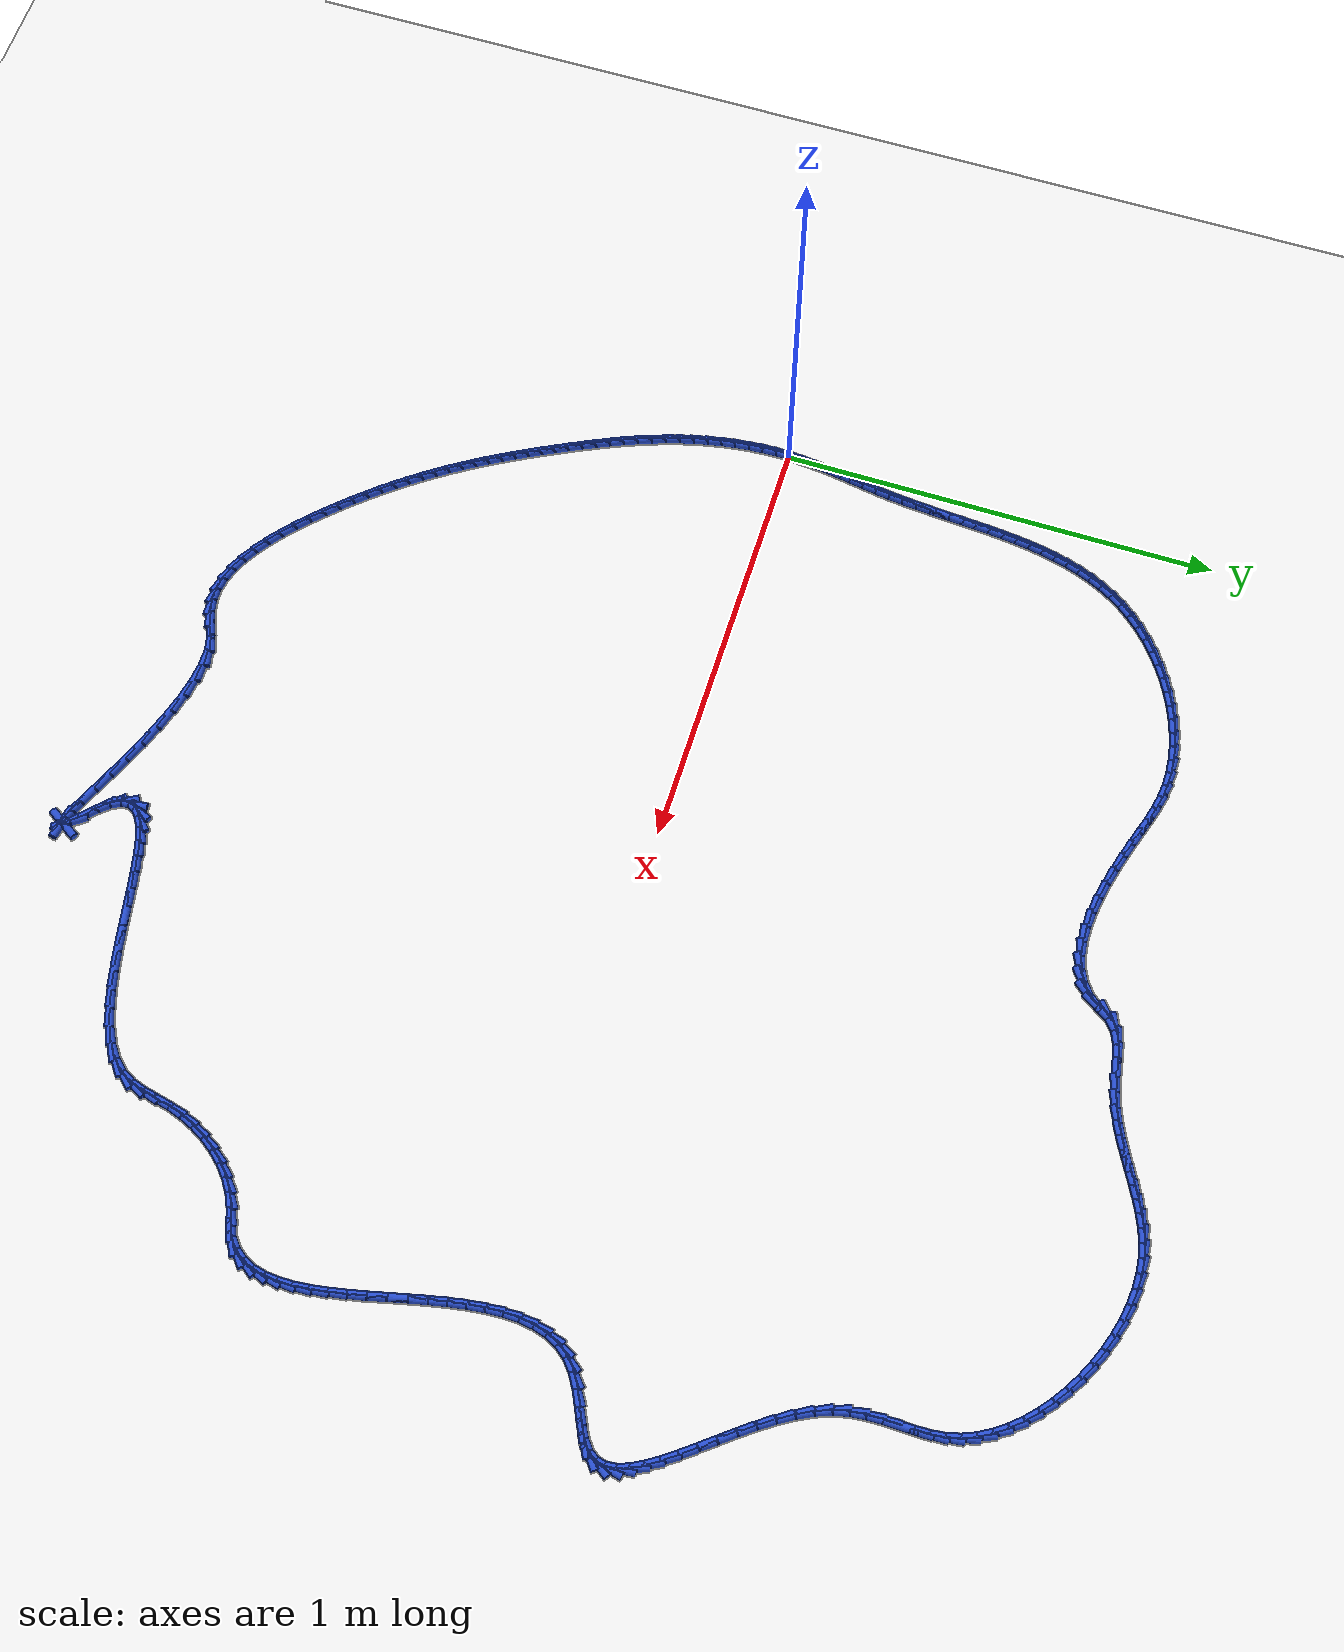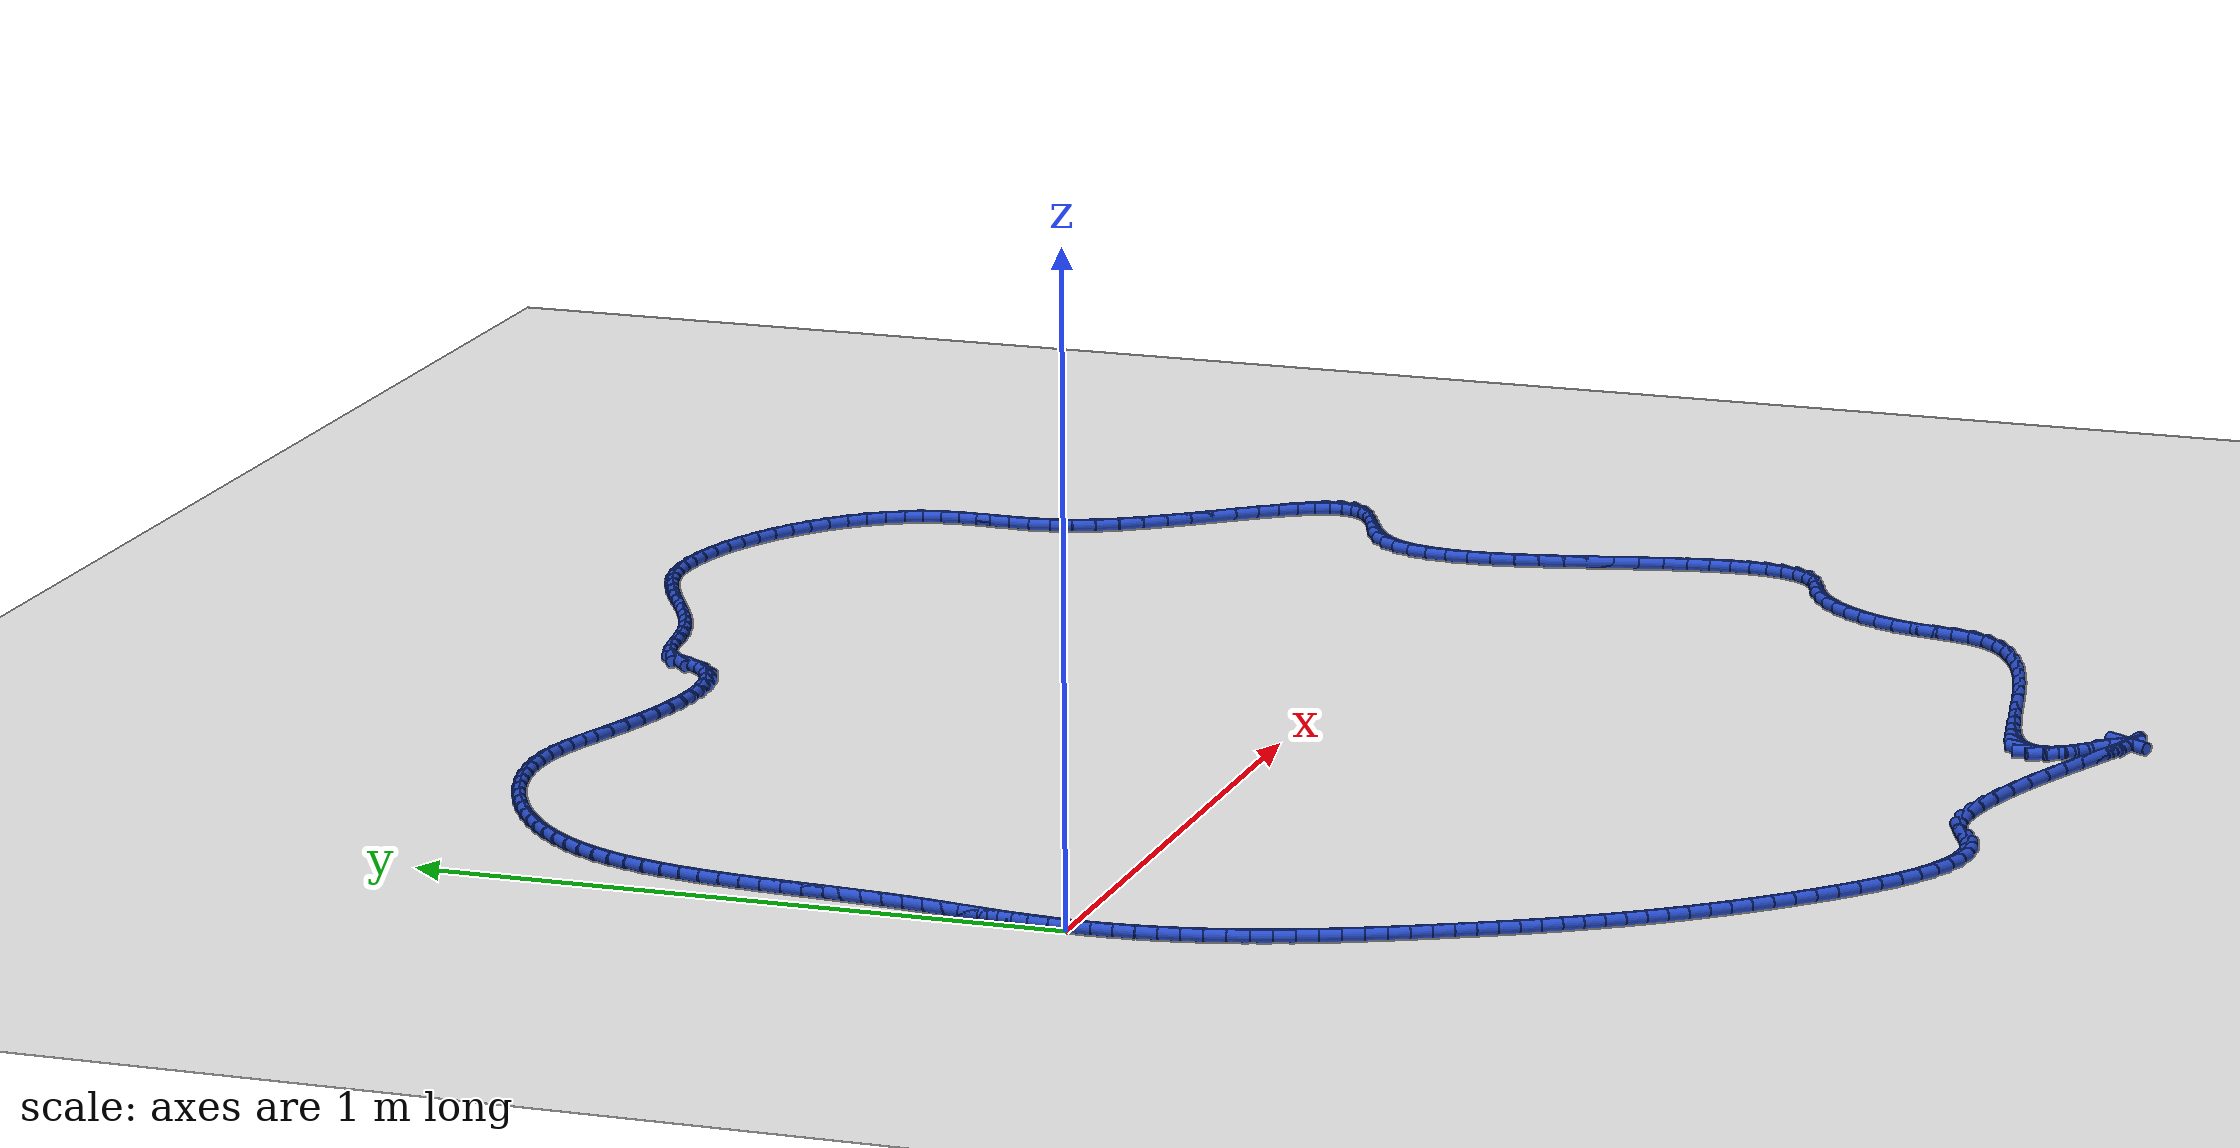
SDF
<sdf version="1.6">
 <world name="default">
  <light name="sun" type="directional">
   <pose>0 0 10 0 -0 0</pose>
   <diffuse>0.8 0.8 0.8 1</diffuse>
   <specular>0.2 0.2 0.2 1</specular>
   <attenuation>
    <range>1000</range>
    <constant>0.9</constant>
    <linear>0.01</linear>
    <quadratic>0.001</quadratic>
   </attenuation>
   <direction>-0.5 0.1 -0.9</direction>
  </light>
  <model name="ground_plane">
   <static>1</static>
   <link name="link">
    <collision name="collision">
     <geometry><plane><normal>0 0 1</normal><size>100 100</size></plane></geometry>
     <surface><friction><ode><mu>100</mu><mu2>50</mu2></ode></friction></surface>
    </collision>
    <visual name="visual">
     <cast_shadows>0</cast_shadows>
     <geometry><plane><normal>0 0 1</normal><size>100 100</size></plane></geometry>
     <material>
      <script><uri>file://media/materials/scripts/gazebo.material</uri><name>Gazebo/WhiteGlow</name></script>
     </material>
    </visual>
   </link>
  </model>
  <gravity>0 0 -9.8</gravity>
  <magnetic_field>6e-06 2.3e-05 -4.2e-05</magnetic_field>
  <atmosphere type="adiabatic"/>
  <physics name="default_physics" default="0" type="ode">
   <max_step_size>0.001</max_step_size>
   <real_time_factor>1</real_time_factor>
   <real_time_update_rate>1000</real_time_update_rate>
  </physics>
  <scene><ambient>0.4 0.4 0.4 1</ambient><background>0.7 0.7 0.7 1</background><shadows>1</shadows></scene>
  <spherical_coordinates>
   <surface_model>EARTH_WGS84</surface_model>
   <latitude_deg>0</latitude_deg>
   <longitude_deg>0</longitude_deg>
   <elevation>0</elevation>
   <heading_deg>0</heading_deg>
  </spherical_coordinates>
  <model name="line">
   <link name="link_0">
    <pose>1.734723475976807e-18 7.632783294297951e-17 0.01 0 1.57 1.5088606404319338</pose>
    <collision name="collision">
     <geometry><cylinder><radius>0.01</radius><length>0.08</length></cylinder></geometry>
    </collision>
    <visual name="visual">
     <material>
      <script><name>Gazebo/Blue</name><uri>file://media/materials/scripts/gazebo.material</uri></script>
     </material>
     <geometry><cylinder><radius>0.01</radius><length>0.08</length></cylinder></geometry>
    </visual>
   </link>
   <link name="link_1">
    <pose>0.0019814948646000507 0.03195186235705555 0.01 0 1.57 1.4710465922923714</pose>
    <collision name="collision">
     <geometry><cylinder><radius>0.01</radius><length>0.08</length></cylinder></geometry>
    </collision>
    <visual name="visual">
     <material>
      <script><name>Gazebo/Blue</name><uri>file://media/materials/scripts/gazebo.material</uri></script>
     </material>
     <geometry><cylinder><radius>0.01</radius><length>0.08</length></cylinder></geometry>
    </visual>
   </link>
   <link name="link_2">
    <pose>0.005168089136434301 0.06379173029452886 0.01 0 1.57 1.4422814226991718</pose>
    <collision name="collision">
     <geometry><cylinder><radius>0.01</radius><length>0.08</length></cylinder></geometry>
    </collision>
    <visual name="visual">
     <material>
      <script><name>Gazebo/Blue</name><uri>file://media/materials/scripts/gazebo.material</uri></script>
     </material>
     <geometry><cylinder><radius>0.01</radius><length>0.08</length></cylinder></geometry>
    </visual>
   </link>
   <link name="link_3">
    <pose>0.009276603302800146 0.09558469937118494 0.01 0 1.57 1.4226572362010865</pose>
    <collision name="collision">
     <geometry><cylinder><radius>0.01</radius><length>0.08</length></cylinder></geometry>
    </collision>
    <visual name="visual">
     <material>
      <script><name>Gazebo/Blue</name><uri>file://media/materials/scripts/gazebo.material</uri></script>
     </material>
     <geometry><cylinder><radius>0.01</radius><length>0.08</length></cylinder></geometry>
    </visual>
   </link>
   <link name="link_4">
    <pose>0.014023857850994949 0.1273958651457886 0.01 0 1.57 1.4121501706744255</pose>
    <collision name="collision">
     <geometry><cylinder><radius>0.01</radius><length>0.08</length></cylinder></geometry>
    </collision>
    <visual name="visual">
     <material>
      <script><name>Gazebo/Blue</name><uri>file://media/materials/scripts/gazebo.material</uri></script>
     </material>
     <geometry><cylinder><radius>0.01</radius><length>0.08</length></cylinder></geometry>
    </visual>
   </link>
   <link name="link_5">
    <pose>0.0191266732683161 0.15929032317710473 0.01 0 1.57 1.4106704192429702</pose>
    <collision name="collision">
     <geometry><cylinder><radius>0.01</radius><length>0.08</length></cylinder></geometry>
    </collision>
    <visual name="visual">
     <material>
      <script><name>Gazebo/Blue</name><uri>file://media/materials/scripts/gazebo.material</uri></script>
     </material>
     <geometry><cylinder><radius>0.01</radius><length>0.08</length></cylinder></geometry>
    </visual>
   </link>
   <link name="link_6">
    <pose>0.024301870042060976 0.19133316902389833 0.01 0 1.57 1.4180898686334655</pose>
    <collision name="collision">
     <geometry><cylinder><radius>0.01</radius><length>0.08</length></cylinder></geometry>
    </collision>
    <visual name="visual">
     <material>
      <script><name>Gazebo/Blue</name><uri>file://media/materials/scripts/gazebo.material</uri></script>
     </material>
     <geometry><cylinder><radius>0.01</radius><length>0.08</length></cylinder></geometry>
    </visual>
   </link>
   <link name="link_7">
    <pose>0.029266268659526945 0.2235894982449341 0.01 0 1.57 1.434247552276316</pose>
    <collision name="collision">
     <geometry><cylinder><radius>0.01</radius><length>0.08</length></cylinder></geometry>
    </collision>
    <visual name="visual">
     <material>
      <script><name>Gazebo/Blue</name><uri>file://media/materials/scripts/gazebo.material</uri></script>
     </material>
     <geometry><cylinder><radius>0.01</radius><length>0.08</length></cylinder></geometry>
    </visual>
   </link>
   <link name="link_8">
    <pose>0.033736689608011385 0.256124406398977 0.01 0 1.57 1.4570660973408645</pose>
    <collision name="collision">
     <geometry><cylinder><radius>0.01</radius><length>0.08</length></cylinder></geometry>
    </collision>
    <visual name="visual">
     <material>
      <script><name>Gazebo/Blue</name><uri>file://media/materials/scripts/gazebo.material</uri></script>
     </material>
     <geometry><cylinder><radius>0.01</radius><length>0.08</length></cylinder></geometry>
    </visual>
   </link>
   <link name="link_9">
    <pose>0.03749006003651354 0.28898439214546656 0.01 0 1.57 1.476875158580273</pose>
    <collision name="collision">
     <geometry><cylinder><radius>0.01</radius><length>0.08</length></cylinder></geometry>
    </collision>
    <visual name="visual">
     <material>
      <script><name>Gazebo/Blue</name><uri>file://media/materials/scripts/gazebo.material</uri></script>
     </material>
     <geometry><cylinder><radius>0.01</radius><length>0.08</length></cylinder></geometry>
    </visual>
   </link>
   <link name="link_10">
    <pose>0.040611436690684455 0.3221206193685303 0.01 0 1.57 1.4907798391306923</pose>
    <collision name="collision">
     <geometry><cylinder><radius>0.01</radius><length>0.08</length></cylinder></geometry>
    </collision>
    <visual name="visual">
     <material>
      <script><name>Gazebo/Blue</name><uri>file://media/materials/scripts/gazebo.material</uri></script>
     </material>
     <geometry><cylinder><radius>0.01</radius><length>0.08</length></cylinder></geometry>
    </visual>
   </link>
   <link name="link_11">
    <pose>0.043284346556187785 0.35545378542681894 0.01 0 1.57 1.4989335394535366</pose>
    <collision name="collision">
     <geometry><cylinder><radius>0.01</radius><length>0.08</length></cylinder></geometry>
    </collision>
    <visual name="visual">
     <material>
      <script><name>Gazebo/Blue</name><uri>file://media/materials/scripts/gazebo.material</uri></script>
     </material>
     <geometry><cylinder><radius>0.01</radius><length>0.08</length></cylinder></geometry>
    </visual>
   </link>
   <link name="link_12">
    <pose>0.045692360108552314 0.3889045742232927 0.01 0 1.57 1.501431809270613</pose>
    <collision name="collision">
     <geometry><cylinder><radius>0.01</radius><length>0.08</length></cylinder></geometry>
    </collision>
    <visual name="visual">
     <material>
      <script><name>Gazebo/Blue</name><uri>file://media/materials/scripts/gazebo.material</uri></script>
     </material>
     <geometry><cylinder><radius>0.01</radius><length>0.08</length></cylinder></geometry>
    </visual>
   </link>
   <link name="link_13">
    <pose>0.04801904782330675 0.42239366966091196 0.01 0 1.57 1.4983055941783265</pose>
    <collision name="collision">
     <geometry><cylinder><radius>0.01</radius><length>0.08</length></cylinder></geometry>
    </collision>
    <visual name="visual">
     <material>
      <script><name>Gazebo/Blue</name><uri>file://media/materials/scripts/gazebo.material</uri></script>
     </material>
     <geometry><cylinder><radius>0.01</radius><length>0.08</length></cylinder></geometry>
    </visual>
   </link>
   <link name="link_14">
    <pose>0.05044798017597986 0.4558417556426367 0.01 0 1.57 1.4895197265518316</pose>
    <collision name="collision">
     <geometry><cylinder><radius>0.01</radius><length>0.08</length></cylinder></geometry>
    </collision>
    <visual name="visual">
     <material>
      <script><name>Gazebo/Blue</name><uri>file://media/materials/scripts/gazebo.material</uri></script>
     </material>
     <geometry><cylinder><radius>0.01</radius><length>0.08</length></cylinder></geometry>
    </visual>
   </link>
   <link name="link_15">
    <pose>0.05316272764210035 0.4891695160714271 0.01 0 1.57 1.4749749547206474</pose>
    <collision name="collision">
     <geometry><cylinder><radius>0.01</radius><length>0.08</length></cylinder></geometry>
    </collision>
    <visual name="visual">
     <material>
      <script><name>Gazebo/Blue</name><uri>file://media/materials/scripts/gazebo.material</uri></script>
     </material>
     <geometry><cylinder><radius>0.01</radius><length>0.08</length></cylinder></geometry>
    </visual>
   </link>
   <link name="link_16">
    <pose>0.05634686069719698 0.5222976348502436 0.01 0 1.57 1.4545139357520702</pose>
    <collision name="collision">
     <geometry><cylinder><radius>0.01</radius><length>0.08</length></cylinder></geometry>
    </collision>
    <visual name="visual">
     <material>
      <script><name>Gazebo/Blue</name><uri>file://media/materials/scripts/gazebo.material</uri></script>
     </material>
     <geometry><cylinder><radius>0.01</radius><length>0.08</length></cylinder></geometry>
    </visual>
   </link>
   <link name="link_17">
    <pose>0.06018394981679849 0.5551467958820463 0.01 0 1.57 1.4279323921423728</pose>
    <collision name="collision">
     <geometry><cylinder><radius>0.01</radius><length>0.08</length></cylinder></geometry>
    </collision>
    <visual name="visual">
     <material>
      <script><name>Gazebo/Blue</name><uri>file://media/materials/scripts/gazebo.material</uri></script>
     </material>
     <geometry><cylinder><radius>0.01</radius><length>0.08</length></cylinder></geometry>
    </visual>
   </link>
   <link name="link_18">
    <pose>0.0648575654764336 0.5876376830697954 0.01 0 1.57 1.39499736995248</pose>
    <collision name="collision">
     <geometry><cylinder><radius>0.01</radius><length>0.08</length></cylinder></geometry>
    </collision>
    <visual name="visual">
     <material>
      <script><name>Gazebo/Blue</name><uri>file://media/materials/scripts/gazebo.material</uri></script>
     </material>
     <geometry><cylinder><radius>0.01</radius><length>0.08</length></cylinder></geometry>
    </visual>
   </link>
   <link name="link_19">
    <pose>0.07055127815163106 0.6196909803164511 0.01 0 1.57 1.3554751047346427</pose>
    <collision name="collision">
     <geometry><cylinder><radius>0.01</radius><length>0.08</length></cylinder></geometry>
    </collision>
    <visual name="visual">
     <material>
      <script><name>Gazebo/Blue</name><uri>file://media/materials/scripts/gazebo.material</uri></script>
     </material>
     <geometry><cylinder><radius>0.01</radius><length>0.08</length></cylinder></geometry>
    </visual>
   </link>
   <link name="link_20">
    <pose>0.0774486583179196 0.6512273715249736 0.01 0 1.57 1.3091711000157784</pose>
    <collision name="collision">
     <geometry><cylinder><radius>0.01</radius><length>0.08</length></cylinder></geometry>
    </collision>
    <visual name="visual">
     <material>
      <script><name>Gazebo/Blue</name><uri>file://media/materials/scripts/gazebo.material</uri></script>
     </material>
     <geometry><cylinder><radius>0.01</radius><length>0.08</length></cylinder></geometry>
    </visual>
   </link>
   <link name="link_21">
    <pose>0.08573327645082796 0.682167540598323 0.01 0 1.57 1.255984119481212</pose>
    <collision name="collision">
     <geometry><cylinder><radius>0.01</radius><length>0.08</length></cylinder></geometry>
    </collision>
    <visual name="visual">
     <material>
      <script><name>Gazebo/Blue</name><uri>file://media/materials/scripts/gazebo.material</uri></script>
     </material>
     <geometry><cylinder><radius>0.01</radius><length>0.08</length></cylinder></geometry>
    </visual>
   </link>
   <link name="link_22">
    <pose>0.09558870302588487 0.7124321714394595 0.01 0 1.57 1.1959731708138204</pose>
    <collision name="collision">
     <geometry><cylinder><radius>0.01</radius><length>0.08</length></cylinder></geometry>
    </collision>
    <visual name="visual">
     <material>
      <script><name>Gazebo/Blue</name><uri>file://media/materials/scripts/gazebo.material</uri></script>
     </material>
     <geometry><cylinder><radius>0.01</radius><length>0.08</length></cylinder></geometry>
    </visual>
   </link>
   <link name="link_23">
    <pose>0.10719850851861909 0.7419419479513438 0.01 0 1.57 1.1294316204945463</pose>
    <collision name="collision">
     <geometry><cylinder><radius>0.01</radius><length>0.08</length></cylinder></geometry>
    </collision>
    <visual name="visual">
     <material>
      <script><name>Gazebo/Blue</name><uri>file://media/materials/scripts/gazebo.material</uri></script>
     </material>
     <geometry><cylinder><radius>0.01</radius><length>0.08</length></cylinder></geometry>
    </visual>
   </link>
   <link name="link_24">
    <pose>0.1207462634045594 0.7706175540369357 0.01 0 1.57 1.0569555777172843</pose>
    <collision name="collision">
     <geometry><cylinder><radius>0.01</radius><length>0.08</length></cylinder></geometry>
    </collision>
    <visual name="visual">
     <material>
      <script><name>Gazebo/Blue</name><uri>file://media/materials/scripts/gazebo.material</uri></script>
     </material>
     <geometry><cylinder><radius>0.01</radius><length>0.08</length></cylinder></geometry>
    </visual>
   </link>
   <link name="link_25">
    <pose>0.1364155381592344 0.7983796735991951 0.01 0 1.57 0.979486730409254</pose>
    <collision name="collision">
     <geometry><cylinder><radius>0.01</radius><length>0.08</length></cylinder></geometry>
    </collision>
    <visual name="visual">
     <material>
      <script><name>Gazebo/Blue</name><uri>file://media/materials/scripts/gazebo.material</uri></script>
     </material>
     <geometry><cylinder><radius>0.01</radius><length>0.08</length></cylinder></geometry>
    </visual>
   </link>
   <link name="link_26">
    <pose>0.15438990325817295 0.8251489905410829 0.01 0 1.57 0.8994100275130474</pose>
    <collision name="collision">
     <geometry><cylinder><radius>0.01</radius><length>0.08</length></cylinder></geometry>
    </collision>
    <visual name="visual">
     <material>
      <script><name>Gazebo/Blue</name><uri>file://media/materials/scripts/gazebo.material</uri></script>
     </material>
     <geometry><cylinder><radius>0.01</radius><length>0.08</length></cylinder></geometry>
    </visual>
   </link>
   <link name="link_27">
    <pose>0.17480095725403763 0.8508390065336188 0.01 0 1.57 0.823158644717444</pose>
    <collision name="collision">
     <geometry><cylinder><radius>0.01</radius><length>0.08</length></cylinder></geometry>
    </collision>
    <visual name="visual">
     <material>
      <script><name>Gazebo/Blue</name><uri>file://media/materials/scripts/gazebo.material</uri></script>
     </material>
     <geometry><cylinder><radius>0.01</radius><length>0.08</length></cylinder></geometry>
    </visual>
   </link>
   <link name="link_28">
    <pose>0.19750428889256885 0.8753250802209427 0.01 0 1.57 0.751697193000518</pose>
    <collision name="collision">
     <geometry><cylinder><radius>0.01</radius><length>0.08</length></cylinder></geometry>
    </collision>
    <visual name="visual">
     <material>
      <script><name>Gazebo/Blue</name><uri>file://media/materials/scripts/gazebo.material</uri></script>
     </material>
     <geometry><cylinder><radius>0.01</radius><length>0.08</length></cylinder></geometry>
    </visual>
   </link>
   <link name="link_29">
    <pose>0.2222642155685694 0.8984699570519189 0.01 0 1.57 0.683890236731315</pose>
    <collision name="collision">
     <geometry><cylinder><radius>0.01</radius><length>0.08</length></cylinder></geometry>
    </collision>
    <visual name="visual">
     <material>
      <script><name>Gazebo/Blue</name><uri>file://media/materials/scripts/gazebo.material</uri></script>
     </material>
     <geometry><cylinder><radius>0.01</radius><length>0.08</length></cylinder></geometry>
    </visual>
   </link>
   <link name="link_30">
    <pose>0.24884499663010615 0.9201363744536752 0.01 0 1.57 0.6186537151266341</pose>
    <collision name="collision">
     <geometry><cylinder><radius>0.01</radius><length>0.08</length></cylinder></geometry>
    </collision>
    <visual name="visual">
     <material>
      <script><name>Gazebo/Blue</name><uri>file://media/materials/scripts/gazebo.material</uri></script>
     </material>
     <geometry><cylinder><radius>0.01</radius><length>0.08</length></cylinder></geometry>
    </visual>
   </link>
   <link name="link_31">
    <pose>0.2770108914252454 0.9401870698533387 0.01 0 1.57 0.5549527693007458</pose>
    <collision name="collision">
     <geometry><cylinder><radius>0.01</radius><length>0.08</length></cylinder></geometry>
    </collision>
    <visual name="visual">
     <material>
      <script><name>Gazebo/Blue</name><uri>file://media/materials/scripts/gazebo.material</uri></script>
     </material>
     <geometry><cylinder><radius>0.01</radius><length>0.08</length></cylinder></geometry>
    </visual>
   </link>
   <link name="link_32">
    <pose>0.3065261593020542 0.9584847806780372 0.01 0 1.57 0.4917869587413772</pose>
    <collision name="collision">
     <geometry><cylinder><radius>0.01</radius><length>0.08</length></cylinder></geometry>
    </collision>
    <visual name="visual">
     <material>
      <script><name>Gazebo/Blue</name><uri>file://media/materials/scripts/gazebo.material</uri></script>
     </material>
     <geometry><cylinder><radius>0.01</radius><length>0.08</length></cylinder></geometry>
    </visual>
   </link>
   <link name="link_33">
    <pose>0.3371550596085989 0.9748922443548979 0.01 0 1.57 0.42817007842313104</pose>
    <collision name="collision">
     <geometry><cylinder><radius>0.01</radius><length>0.08</length></cylinder></geometry>
    </collision>
    <visual name="visual">
     <material>
      <script><name>Gazebo/Blue</name><uri>file://media/materials/scripts/gazebo.material</uri></script>
     </material>
     <geometry><cylinder><radius>0.01</radius><length>0.08</length></cylinder></geometry>
    </visual>
   </link>
   <link name="link_34">
    <pose>0.36866185169294596 0.9892721983110478 0.01 0 1.57 0.36310850138713446</pose>
    <collision name="collision">
     <geometry><cylinder><radius>0.01</radius><length>0.08</length></cylinder></geometry>
    </collision>
    <visual name="visual">
     <material>
      <script><name>Gazebo/Blue</name><uri>file://media/materials/scripts/gazebo.material</uri></script>
     </material>
     <geometry><cylinder><radius>0.01</radius><length>0.08</length></cylinder></geometry>
    </visual>
   </link>
   <link name="link_35">
    <pose>0.40081079490316235 1.0014873799736148 0.01 0 1.57 0.29558127397241796</pose>
    <collision name="collision">
     <geometry><cylinder><radius>0.01</radius><length>0.08</length></cylinder></geometry>
    </collision>
    <visual name="visual">
     <material>
      <script><name>Gazebo/Blue</name><uri>file://media/materials/scripts/gazebo.material</uri></script>
     </material>
     <geometry><cylinder><radius>0.01</radius><length>0.08</length></cylinder></geometry>
    </visual>
   </link>
   <link name="link_36">
    <pose>0.4333661485873144 1.0114005267697264 0.01 0 1.57 0.22452575499002786</pose>
    <collision name="collision">
     <geometry><cylinder><radius>0.01</radius><length>0.08</length></cylinder></geometry>
    </collision>
    <visual name="visual">
     <material>
      <script><name>Gazebo/Blue</name><uri>file://media/materials/scripts/gazebo.material</uri></script>
     </material>
     <geometry><cylinder><radius>0.01</radius><length>0.08</length></cylinder></geometry>
    </visual>
   </link>
   <link name="link_37">
    <pose>0.4660921720934691 1.0188743761265096 0.01 0 1.57 0.14883444449405683</pose>
    <collision name="collision">
     <geometry><cylinder><radius>0.01</radius><length>0.08</length></cylinder></geometry>
    </collision>
    <visual name="visual">
     <material>
      <script><name>Gazebo/Blue</name><uri>file://media/materials/scripts/gazebo.material</uri></script>
     </material>
     <geometry><cylinder><radius>0.01</radius><length>0.08</length></cylinder></geometry>
    </visual>
   </link>
   <link name="link_38">
    <pose>0.49875312476969247 1.023771665471092 0.01 0 1.57 0.06737183830236193</pose>
    <collision name="collision">
     <geometry><cylinder><radius>0.01</radius><length>0.08</length></cylinder></geometry>
    </collision>
    <visual name="visual">
     <material>
      <script><name>Gazebo/Blue</name><uri>file://media/materials/scripts/gazebo.material</uri></script>
     </material>
     <geometry><cylinder><radius>0.01</radius><length>0.08</length></cylinder></geometry>
    </visual>
   </link>
   <link name="link_39">
    <pose>0.5311132659640518 1.025955132230601 0.01 0 1.57 -0.020975650541623307</pose>
    <collision name="collision">
     <geometry><cylinder><radius>0.01</radius><length>0.08</length></cylinder></geometry>
    </collision>
    <visual name="visual">
     <material>
      <script><name>Gazebo/Blue</name><uri>file://media/materials/scripts/gazebo.material</uri></script>
     </material>
     <geometry><cylinder><radius>0.01</radius><length>0.08</length></cylinder></geometry>
    </visual>
   </link>
   <link name="link_40">
    <pose>0.5629368550246131 1.025287513832164 0.01 0 1.57 -0.11682227531001083</pose>
    <collision name="collision">
     <geometry><cylinder><radius>0.01</radius><length>0.08</length></cylinder></geometry>
    </collision>
    <visual name="visual">
     <material>
      <script><name>Gazebo/Blue</name><uri>file://media/materials/scripts/gazebo.material</uri></script>
     </material>
     <geometry><cylinder><radius>0.01</radius><length>0.08</length></cylinder></geometry>
    </visual>
   </link>
   <link name="link_41">
    <pose>0.5940001245094084 1.0216420330727671 0.01 0 1.57 -0.20685831782249942</pose>
    <collision name="collision">
     <geometry><cylinder><radius>0.01</radius><length>0.08</length></cylinder></geometry>
    </collision>
    <visual name="visual">
     <material>
      <script><name>Gazebo/Blue</name><uri>file://media/materials/scripts/gazebo.material</uri></script>
     </material>
     <geometry><cylinder><radius>0.01</radius><length>0.08</length></cylinder></geometry>
    </visual>
   </link>
   <link name="link_42">
    <pose>0.624482492244297 1.0152449965646024 0.01 0 1.57 -0.27097365908186444</pose>
    <collision name="collision">
     <geometry><cylinder><radius>0.01</radius><length>0.08</length></cylinder></geometry>
    </collision>
    <visual name="visual">
     <material>
      <script><name>Gazebo/Blue</name><uri>file://media/materials/scripts/gazebo.material</uri></script>
     </material>
     <geometry><cylinder><radius>0.01</radius><length>0.08</length></cylinder></geometry>
    </visual>
   </link>
   <link name="link_43">
    <pose>0.6550537055359185 1.0067521100512224 0.01 0 1.57 -0.3059984752589177</pose>
    <collision name="collision">
     <geometry><cylinder><radius>0.01</radius><length>0.08</length></cylinder></geometry>
    </collision>
    <visual name="visual">
     <material>
      <script><name>Gazebo/Blue</name><uri>file://media/materials/scripts/gazebo.material</uri></script>
     </material>
     <geometry><cylinder><radius>0.01</radius><length>0.08</length></cylinder></geometry>
    </visual>
   </link>
   <link name="link_44">
    <pose>0.6864131232162729 0.9968450111521242 0.01 0 1.57 -0.313256914609435</pose>
    <collision name="collision">
     <geometry><cylinder><radius>0.01</radius><length>0.08</length></cylinder></geometry>
    </collision>
    <visual name="visual">
     <material>
      <script><name>Gazebo/Blue</name><uri>file://media/materials/scripts/gazebo.material</uri></script>
     </material>
     <geometry><cylinder><radius>0.01</radius><length>0.08</length></cylinder></geometry>
    </visual>
   </link>
   <link name="link_45">
    <pose>0.7192596535509933 0.9862052850712042 0.01 0 1.57 -0.2995371547147501</pose>
    <collision name="collision">
     <geometry><cylinder><radius>0.01</radius><length>0.08</length></cylinder></geometry>
    </collision>
    <visual name="visual">
     <material>
      <script><name>Gazebo/Blue</name><uri>file://media/materials/scripts/gazebo.material</uri></script>
     </material>
     <geometry><cylinder><radius>0.01</radius><length>0.08</length></cylinder></geometry>
    </visual>
   </link>
   <link name="link_46">
    <pose>0.7539904226080872 0.9754794098742945 0.01 0 1.57 -0.2763118029908803</pose>
    <collision name="collision">
     <geometry><cylinder><radius>0.01</radius><length>0.08</length></cylinder></geometry>
    </collision>
    <visual name="visual">
     <material>
      <script><name>Gazebo/Blue</name><uri>file://media/materials/scripts/gazebo.material</uri></script>
     </material>
     <geometry><cylinder><radius>0.01</radius><length>0.08</length></cylinder></geometry>
    </visual>
   </link>
   <link name="link_47">
    <pose>0.790177813029124 0.9652179189970741 0.01 0 1.57 -0.24481662532636664</pose>
    <collision name="collision">
     <geometry><cylinder><radius>0.01</radius><length>0.08</length></cylinder></geometry>
    </collision>
    <visual name="visual">
     <material>
      <script><name>Gazebo/Blue</name><uri>file://media/materials/scripts/gazebo.material</uri></script>
     </material>
     <geometry><cylinder><radius>0.01</radius><length>0.08</length></cylinder></geometry>
    </visual>
   </link>
   <link name="link_48">
    <pose>0.8272546009942077 0.9559551050785289 0.01 0 1.57 -0.20381612713430444</pose>
    <collision name="collision">
     <geometry><cylinder><radius>0.01</radius><length>0.08</length></cylinder></geometry>
    </collision>
    <visual name="visual">
     <material>
      <script><name>Gazebo/Blue</name><uri>file://media/materials/scripts/gazebo.material</uri></script>
     </material>
     <geometry><cylinder><radius>0.01</radius><length>0.08</length></cylinder></geometry>
    </visual>
   </link>
   <link name="link_49">
    <pose>0.8646535626834423 0.9482252607576458 0.01 0 1.57 -0.1512448794798832</pose>
    <collision name="collision">
     <geometry><cylinder><radius>0.01</radius><length>0.08</length></cylinder></geometry>
    </collision>
    <visual name="visual">
     <material>
      <script><name>Gazebo/Blue</name><uri>file://media/materials/scripts/gazebo.material</uri></script>
     </material>
     <geometry><cylinder><radius>0.01</radius><length>0.08</length></cylinder></geometry>
    </visual>
   </link>
   <link name="link_50">
    <pose>0.9018074742769316 0.9425626786734103 0.01 0 1.57 -0.08403085780598142</pose>
    <collision name="collision">
     <geometry><cylinder><radius>0.01</radius><length>0.08</length></cylinder></geometry>
    </collision>
    <visual name="visual">
     <material>
      <script><name>Gazebo/Blue</name><uri>file://media/materials/scripts/gazebo.material</uri></script>
     </material>
     <geometry><cylinder><radius>0.01</radius><length>0.08</length></cylinder></geometry>
    </visual>
   </link>
   <link name="link_51">
    <pose>0.9381491119547798 0.9395016514648082 0.01 0 1.57 0.002140034675275217</pose>
    <collision name="collision">
     <geometry><cylinder><radius>0.01</radius><length>0.08</length></cylinder></geometry>
    </collision>
    <visual name="visual">
     <material>
      <script><name>Gazebo/Blue</name><uri>file://media/materials/scripts/gazebo.material</uri></script>
     </material>
     <geometry><cylinder><radius>0.01</radius><length>0.08</length></cylinder></geometry>
    </visual>
   </link>
   <link name="link_52">
    <pose>0.9731112518970908 0.939576471770826 0.01 0 1.57 0.11294788858068389</pose>
    <collision name="collision">
     <geometry><cylinder><radius>0.01</radius><length>0.08</length></cylinder></geometry>
    </collision>
    <visual name="visual">
     <material>
      <script><name>Gazebo/Blue</name><uri>file://media/materials/scripts/gazebo.material</uri></script>
     </material>
     <geometry><cylinder><radius>0.01</radius><length>0.08</length></cylinder></geometry>
    </visual>
   </link>
   <link name="link_53">
    <pose>1.0061266702839684 0.9433214322304502 0.01 0 1.57 0.2549517628960885</pose>
    <collision name="collision">
     <geometry><cylinder><radius>0.01</radius><length>0.08</length></cylinder></geometry>
    </collision>
    <visual name="visual">
     <material>
      <script><name>Gazebo/Blue</name><uri>file://media/materials/scripts/gazebo.material</uri></script>
     </material>
     <geometry><cylinder><radius>0.01</radius><length>0.08</length></cylinder></geometry>
    </visual>
   </link>
   <link name="link_54">
    <pose>1.0366281432955171 0.9512708254826658 0.01 0 1.57 0.4333872648068971</pose>
    <collision name="collision">
     <geometry><cylinder><radius>0.01</radius><length>0.08</length></cylinder></geometry>
    </collision>
    <visual name="visual">
     <material>
      <script><name>Gazebo/Blue</name><uri>file://media/materials/scripts/gazebo.material</uri></script>
     </material>
     <geometry><cylinder><radius>0.01</radius><length>0.08</length></cylinder></geometry>
    </visual>
   </link>
   <link name="link_55">
    <pose>1.0640484471118403 0.9639589441664599 0.01 0 1.57 0.6470508748743125</pose>
    <collision name="collision">
     <geometry><cylinder><radius>0.01</radius><length>0.08</length></cylinder></geometry>
    </collision>
    <visual name="visual">
     <material>
      <script><name>Gazebo/Blue</name><uri>file://media/materials/scripts/gazebo.material</uri></script>
     </material>
     <geometry><cylinder><radius>0.01</radius><length>0.08</length></cylinder></geometry>
    </visual>
   </link>
   <link name="link_56">
    <pose>1.0878203579130425 0.9819200809208182 0.01 0 1.57 0.8823163824602731</pose>
    <collision name="collision">
     <geometry><cylinder><radius>0.01</radius><length>0.08</length></cylinder></geometry>
    </collision>
    <visual name="visual">
     <material>
      <script><name>Gazebo/Blue</name><uri>file://media/materials/scripts/gazebo.material</uri></script>
     </material>
     <geometry><cylinder><radius>0.01</radius><length>0.08</length></cylinder></geometry>
    </visual>
   </link>
   <link name="link_57">
    <pose>1.1073766518792274 1.0056885283847263 0.01 0 1.57 1.0067197105359778</pose>
    <collision name="collision">
     <geometry><cylinder><radius>0.01</radius><length>0.08</length></cylinder></geometry>
    </collision>
    <visual name="visual">
     <material>
      <script><name>Gazebo/Blue</name><uri>file://media/materials/scripts/gazebo.material</uri></script>
     </material>
     <geometry><cylinder><radius>0.01</radius><length>0.08</length></cylinder></geometry>
    </visual>
   </link>
   <link name="link_58">
    <pose>1.124518140577839 1.0327835656216062 0.01 0 1.57 0.695245705959541</pose>
    <collision name="collision">
     <geometry><cylinder><radius>0.01</radius><length>0.08</length></cylinder></geometry>
    </collision>
    <visual name="visual">
     <material>
      <script><name>Gazebo/Blue</name><uri>file://media/materials/scripts/gazebo.material</uri></script>
     </material>
     <geometry><cylinder><radius>0.01</radius><length>0.08</length></cylinder></geometry>
    </visual>
   </link>
   <link name="link_59">
    <pose>1.1478004280402363 1.0522054986900038 0.01 0 1.57 0.39499429178639595</pose>
    <collision name="collision">
     <geometry><cylinder><radius>0.01</radius><length>0.08</length></cylinder></geometry>
    </collision>
    <visual name="visual">
     <material>
      <script><name>Gazebo/Blue</name><uri>file://media/materials/scripts/gazebo.material</uri></script>
     </material>
     <geometry><cylinder><radius>0.01</radius><length>0.08</length></cylinder></geometry>
    </visual>
   </link>
   <link name="link_60">
    <pose>1.176968419094043 1.0643657838468366 0.01 0 1.57 0.22753120355289683</pose>
    <collision name="collision">
     <geometry><cylinder><radius>0.01</radius><length>0.08</length></cylinder></geometry>
    </collision>
    <visual name="visual">
     <material>
      <script><name>Gazebo/Blue</name><uri>file://media/materials/scripts/gazebo.material</uri></script>
     </material>
     <geometry><cylinder><radius>0.01</radius><length>0.08</length></cylinder></geometry>
    </visual>
   </link>
   <link name="link_61">
    <pose>1.2099597006858465 1.072004608873415 0.01 0 1.57 0.166982682259189</pose>
    <collision name="collision">
     <geometry><cylinder><radius>0.01</radius><length>0.08</length></cylinder></geometry>
    </collision>
    <visual name="visual">
     <material>
      <script><name>Gazebo/Blue</name><uri>file://media/materials/scripts/gazebo.material</uri></script>
     </material>
     <geometry><cylinder><radius>0.01</radius><length>0.08</length></cylinder></geometry>
    </visual>
   </link>
   <link name="link_62">
    <pose>1.2447118597622349 1.0778621615510502 0.01 0 1.57 0.19516450393243365</pose>
    <collision name="collision">
     <geometry><cylinder><radius>0.01</radius><length>0.08</length></cylinder></geometry>
    </collision>
    <visual name="visual">
     <material>
      <script><name>Gazebo/Blue</name><uri>file://media/materials/scripts/gazebo.material</uri></script>
     </material>
     <geometry><cylinder><radius>0.01</radius><length>0.08</length></cylinder></geometry>
    </visual>
   </link>
   <link name="link_63">
    <pose>1.2791663748809057 1.0846731553507563 0.01 0 1.57 0.28268416763427084</pose>
    <collision name="collision">
     <geometry><cylinder><radius>0.01</radius><length>0.08</length></cylinder></geometry>
    </collision>
    <visual name="visual">
     <material>
      <script><name>Gazebo/Blue</name><uri>file://media/materials/scripts/gazebo.material</uri></script>
     </material>
     <geometry><cylinder><radius>0.01</radius><length>0.08</length></cylinder></geometry>
    </visual>
   </link>
   <link name="link_64">
    <pose>1.3119575154048235 1.0941977583093248 0.01 0 1.57 0.36412488224008605</pose>
    <collision name="collision">
     <geometry><cylinder><radius>0.01</radius><length>0.08</length></cylinder></geometry>
    </collision>
    <visual name="visual">
     <material>
      <script><name>Gazebo/Blue</name><uri>file://media/materials/scripts/gazebo.material</uri></script>
     </material>
     <geometry><cylinder><radius>0.01</radius><length>0.08</length></cylinder></geometry>
    </visual>
   </link>
   <link name="link_65">
    <pose>1.3432048771643088 1.106106736993317 0.01 0 1.57 0.42803171538979967</pose>
    <collision name="collision">
     <geometry><cylinder><radius>0.01</radius><length>0.08</length></cylinder></geometry>
    </collision>
    <visual name="visual">
     <material>
      <script><name>Gazebo/Blue</name><uri>file://media/materials/scripts/gazebo.material</uri></script>
     </material>
     <geometry><cylinder><radius>0.01</radius><length>0.08</length></cylinder></geometry>
    </visual>
   </link>
   <link name="link_66">
    <pose>1.3732199935374312 1.1198008603605032 0.01 0 1.57 0.4727575275970164</pose>
    <collision name="collision">
     <geometry><cylinder><radius>0.01</radius><length>0.08</length></cylinder></geometry>
    </collision>
    <visual name="visual">
     <material>
      <script><name>Gazebo/Blue</name><uri>file://media/materials/scripts/gazebo.material</uri></script>
     </material>
     <geometry><cylinder><radius>0.01</radius><length>0.08</length></cylinder></geometry>
    </visual>
   </link>
   <link name="link_67">
    <pose>1.402314397902258 1.134680897368652 0.01 0 1.57 0.49743250000228273</pose>
    <collision name="collision">
     <geometry><cylinder><radius>0.01</radius><length>0.08</length></cylinder></geometry>
    </collision>
    <visual name="visual">
     <material>
      <script><name>Gazebo/Blue</name><uri>file://media/materials/scripts/gazebo.material</uri></script>
     </material>
     <geometry><cylinder><radius>0.01</radius><length>0.08</length></cylinder></geometry>
    </visual>
   </link>
   <link name="link_68">
    <pose>1.4307996236368603 1.150147616975534 0.01 0 1.57 0.5015076541230402</pose>
    <collision name="collision">
     <geometry><cylinder><radius>0.01</radius><length>0.08</length></cylinder></geometry>
    </collision>
    <visual name="visual">
     <material>
      <script><name>Gazebo/Blue</name><uri>file://media/materials/scripts/gazebo.material</uri></script>
     </material>
     <geometry><cylinder><radius>0.01</radius><length>0.08</length></cylinder></geometry>
    </visual>
   </link>
   <link name="link_69">
    <pose>1.458987204119306 1.1656017881389185 0.01 0 1.57 0.4844644190866808</pose>
    <collision name="collision">
     <geometry><cylinder><radius>0.01</radius><length>0.08</length></cylinder></geometry>
    </collision>
    <visual name="visual">
     <material>
      <script><name>Gazebo/Blue</name><uri>file://media/materials/scripts/gazebo.material</uri></script>
     </material>
     <geometry><cylinder><radius>0.01</radius><length>0.08</length></cylinder></geometry>
    </visual>
   </link>
   <link name="link_70">
    <pose>1.4871886727276653 1.1804441798165752 0.01 0 1.57 0.4457655946768319</pose>
    <collision name="collision">
     <geometry><cylinder><radius>0.01</radius><length>0.08</length></cylinder></geometry>
    </collision>
    <visual name="visual">
     <material>
      <script><name>Gazebo/Blue</name><uri>file://media/materials/scripts/gazebo.material</uri></script>
     </material>
     <geometry><cylinder><radius>0.01</radius><length>0.08</length></cylinder></geometry>
    </visual>
   </link>
   <link name="link_71">
    <pose>1.515715562840006 1.1940755609662739 0.01 0 1.57 0.38509740471232556</pose>
    <collision name="collision">
     <geometry><cylinder><radius>0.01</radius><length>0.08</length></cylinder></geometry>
    </collision>
    <visual name="visual">
     <material>
      <script><name>Gazebo/Blue</name><uri>file://media/materials/scripts/gazebo.material</uri></script>
     </material>
     <geometry><cylinder><radius>0.01</radius><length>0.08</length></cylinder></geometry>
    </visual>
   </link>
   <link name="link_72">
    <pose>1.5448794078343984 1.2058967005457841 0.01 0 1.57 0.30293215008612484</pose>
    <collision name="collision">
     <geometry><cylinder><radius>0.01</radius><length>0.08</length></cylinder></geometry>
    </collision>
    <visual name="visual">
     <material>
      <script><name>Gazebo/Blue</name><uri>file://media/materials/scripts/gazebo.material</uri></script>
     </material>
     <geometry><cylinder><radius>0.01</radius><length>0.08</length></cylinder></geometry>
    </visual>
   </link>
   <link name="link_73">
    <pose>1.5749917410889116 1.215308367512876 0.01 0 1.57 0.20134688348877558</pose>
    <collision name="collision">
     <geometry><cylinder><radius>0.01</radius><length>0.08</length></cylinder></geometry>
    </collision>
    <visual name="visual">
     <material>
      <script><name>Gazebo/Blue</name><uri>file://media/materials/scripts/gazebo.material</uri></script>
     </material>
     <geometry><cylinder><radius>0.01</radius><length>0.08</length></cylinder></geometry>
    </visual>
   </link>
   <link name="link_74">
    <pose>1.6063637032123124 1.2217117817769947 0.01 0 1.57 0.09098231840236612</pose>
    <collision name="collision">
     <geometry><cylinder><radius>0.01</radius><length>0.08</length></cylinder></geometry>
    </collision>
    <visual name="visual">
     <material>
      <script><name>Gazebo/Blue</name><uri>file://media/materials/scripts/gazebo.material</uri></script>
     </material>
     <geometry><cylinder><radius>0.01</radius><length>0.08</length></cylinder></geometry>
    </visual>
   </link>
   <link name="link_75">
    <pose>1.6391377018870636 1.2247018912079866 0.01 0 1.57 -0.009837906757912665</pose>
    <collision name="collision">
     <geometry><cylinder><radius>0.01</radius><length>0.08</length></cylinder></geometry>
    </collision>
    <visual name="visual">
     <material>
      <script><name>Gazebo/Blue</name><uri>file://media/materials/scripts/gazebo.material</uri></script>
     </material>
     <geometry><cylinder><radius>0.01</radius><length>0.08</length></cylinder></geometry>
    </visual>
   </link>
   <link name="link_76">
    <pose>1.6730251363228006 1.2243684990319519 0.01 0 1.57 -0.10037642166458029</pose>
    <collision name="collision">
     <geometry><cylinder><radius>0.01</radius><length>0.08</length></cylinder></geometry>
    </collision>
    <visual name="visual">
     <material>
      <script><name>Gazebo/Blue</name><uri>file://media/materials/scripts/gazebo.material</uri></script>
     </material>
     <geometry><cylinder><radius>0.01</radius><length>0.08</length></cylinder></geometry>
    </visual>
   </link>
   <link name="link_77">
    <pose>1.707669574315302 1.2208792880077244 0.01 0 1.57 -0.1827667809236322</pose>
    <collision name="collision">
     <geometry><cylinder><radius>0.01</radius><length>0.08</length></cylinder></geometry>
    </collision>
    <visual name="visual">
     <material>
      <script><name>Gazebo/Blue</name><uri>file://media/materials/scripts/gazebo.material</uri></script>
     </material>
     <geometry><cylinder><radius>0.01</radius><length>0.08</length></cylinder></geometry>
    </visual>
   </link>
   <link name="link_78">
    <pose>1.7427145836603462 1.214401940894138 0.01 0 1.57 -0.2590237906922626</pose>
    <collision name="collision">
     <geometry><cylinder><radius>0.01</radius><length>0.08</length></cylinder></geometry>
    </collision>
    <visual name="visual">
     <material>
      <script><name>Gazebo/Blue</name><uri>file://media/materials/scripts/gazebo.material</uri></script>
     </material>
     <geometry><cylinder><radius>0.01</radius><length>0.08</length></cylinder></geometry>
    </visual>
   </link>
   <link name="link_79">
    <pose>1.7778037321537112 1.205104140450028 0.01 0 1.57 -0.3309939022233106</pose>
    <collision name="collision">
     <geometry><cylinder><radius>0.01</radius><length>0.08</length></cylinder></geometry>
    </collision>
    <visual name="visual">
     <material>
      <script><name>Gazebo/Blue</name><uri>file://media/materials/scripts/gazebo.material</uri></script>
     </material>
     <geometry><cylinder><radius>0.01</radius><length>0.08</length></cylinder></geometry>
    </visual>
   </link>
   <link name="link_80">
    <pose>1.8125805875911754 1.1931535694342275 0.01 0 1.57 -0.40037234899574076</pose>
    <collision name="collision">
     <geometry><cylinder><radius>0.01</radius><length>0.08</length></cylinder></geometry>
    </collision>
    <visual name="visual">
     <material>
      <script><name>Gazebo/Blue</name><uri>file://media/materials/scripts/gazebo.material</uri></script>
     </material>
     <geometry><cylinder><radius>0.01</radius><length>0.08</length></cylinder></geometry>
    </visual>
   </link>
   <link name="link_81">
    <pose>1.8466887177685185 1.1787179106055712 0.01 0 1.57 -0.46875079803469516</pose>
    <collision name="collision">
     <geometry><cylinder><radius>0.01</radius><length>0.08</length></cylinder></geometry>
    </collision>
    <visual name="visual">
     <material>
      <script><name>Gazebo/Blue</name><uri>file://media/materials/scripts/gazebo.material</uri></script>
     </material>
     <geometry><cylinder><radius>0.01</radius><length>0.08</length></cylinder></geometry>
    </visual>
   </link>
   <link name="link_82">
    <pose>1.8797716904815176 1.161964846722894 0.01 0 1.57 -0.5376770519582957</pose>
    <collision name="collision">
     <geometry><cylinder><radius>0.01</radius><length>0.08</length></cylinder></geometry>
    </collision>
    <visual name="visual">
     <material>
      <script><name>Gazebo/Blue</name><uri>file://media/materials/scripts/gazebo.material</uri></script>
     </material>
     <geometry><cylinder><radius>0.01</radius><length>0.08</length></cylinder></geometry>
    </visual>
   </link>
   <link name="link_83">
    <pose>1.9114730735259509 1.1430620605450286 0.01 0 1.57 -0.6087178557072547</pose>
    <collision name="collision">
     <geometry><cylinder><radius>0.01</radius><length>0.08</length></cylinder></geometry>
    </collision>
    <visual name="visual">
     <material>
      <script><name>Gazebo/Blue</name><uri>file://media/materials/scripts/gazebo.material</uri></script>
     </material>
     <geometry><cylinder><radius>0.01</radius><length>0.08</length></cylinder></geometry>
    </visual>
   </link>
   <link name="link_84">
    <pose>1.9414364346975976 1.122177234830811 0.01 0 1.57 -0.6835191688639457</pose>
    <collision name="collision">
     <geometry><cylinder><radius>0.01</radius><length>0.08</length></cylinder></geometry>
    </collision>
    <visual name="visual">
     <material>
      <script><name>Gazebo/Blue</name><uri>file://media/materials/scripts/gazebo.material</uri></script>
     </material>
     <geometry><cylinder><radius>0.01</radius><length>0.08</length></cylinder></geometry>
    </visual>
   </link>
   <link name="link_85">
    <pose>1.9693053417922368 1.0994780523390741 0.01 0 1.57 -0.7638564646508599</pose>
    <collision name="collision">
     <geometry><cylinder><radius>0.01</radius><length>0.08</length></cylinder></geometry>
    </collision>
    <visual name="visual">
     <material>
      <script><name>Gazebo/Blue</name><uri>file://media/materials/scripts/gazebo.material</uri></script>
     </material>
     <geometry><cylinder><radius>0.01</radius><length>0.08</length></cylinder></geometry>
    </visual>
   </link>
   <link name="link_86">
    <pose>1.9947233626056453 1.075132195828653 0.01 0 1.57 -0.8516602370693729</pose>
    <collision name="collision">
     <geometry><cylinder><radius>0.01</radius><length>0.08</length></cylinder></geometry>
    </collision>
    <visual name="visual">
     <material>
      <script><name>Gazebo/Blue</name><uri>file://media/materials/scripts/gazebo.material</uri></script>
     </material>
     <geometry><cylinder><radius>0.01</radius><length>0.08</length></cylinder></geometry>
    </visual>
   </link>
   <link name="link_87">
    <pose>2.0173340649336025 1.0493073480583819 0.01 0 1.57 -0.9489873049710202</pose>
    <collision name="collision">
     <geometry><cylinder><radius>0.01</radius><length>0.08</length></cylinder></geometry>
    </collision>
    <visual name="visual">
     <material>
      <script><name>Gazebo/Blue</name><uri>file://media/materials/scripts/gazebo.material</uri></script>
     </material>
     <geometry><cylinder><radius>0.01</radius><length>0.08</length></cylinder></geometry>
    </visual>
   </link>
   <link name="link_88">
    <pose>2.036781016571887 1.0221711917870946 0.01 0 1.57 -1.057886133546718</pose>
    <collision name="collision">
     <geometry><cylinder><radius>0.01</radius><length>0.08</length></cylinder></geometry>
    </collision>
    <visual name="visual">
     <material>
      <script><name>Gazebo/Blue</name><uri>file://media/materials/scripts/gazebo.material</uri></script>
     </material>
     <geometry><cylinder><radius>0.01</radius><length>0.08</length></cylinder></geometry>
    </visual>
   </link>
   <link name="link_89">
    <pose>2.052707785316277 0.9938914097736256 0.01 0 1.57 -1.180081775480463</pose>
    <collision name="collision">
     <geometry><cylinder><radius>0.01</radius><length>0.08</length></cylinder></geometry>
    </collision>
    <visual name="visual">
     <material>
      <script><name>Gazebo/Blue</name><uri>file://media/materials/scripts/gazebo.material</uri></script>
     </material>
     <geometry><cylinder><radius>0.01</radius><length>0.08</length></cylinder></geometry>
    </visual>
   </link>
   <link name="link_90">
    <pose>2.064757938962551 0.9646356847768093 0.01 0 1.57 -1.3162960040517326</pose>
    <collision name="collision">
     <geometry><cylinder><radius>0.01</radius><length>0.08</length></cylinder></geometry>
    </collision>
    <visual name="visual">
     <material>
      <script><name>Gazebo/Blue</name><uri>file://media/materials/scripts/gazebo.material</uri></script>
     </material>
     <geometry><cylinder><radius>0.01</radius><length>0.08</length></cylinder></geometry>
    </visual>
   </link>
   <link name="link_91">
    <pose>2.0725788843088875 0.9345714541108952 0.01 0 1.57 -1.4486423006202895</pose>
    <collision name="collision">
     <geometry><cylinder><radius>0.01</radius><length>0.08</length></cylinder></geometry>
    </collision>
    <visual name="visual">
     <material>
      <script><name>Gazebo/Blue</name><uri>file://media/materials/scripts/gazebo.material</uri></script>
     </material>
     <geometry><cylinder><radius>0.01</radius><length>0.08</length></cylinder></geometry>
    </visual>
   </link>
   <link name="link_92">
    <pose>2.0763526241098353 0.9038319759808353 0.01 0 1.57 -1.5393300726159378</pose>
    <collision name="collision">
     <geometry><cylinder><radius>0.01</radius><length>0.08</length></cylinder></geometry>
    </collision>
    <visual name="visual">
     <material>
      <script><name>Gazebo/Blue</name><uri>file://media/materials/scripts/gazebo.material</uri></script>
     </material>
     <geometry><cylinder><radius>0.01</radius><length>0.08</length></cylinder></geometry>
    </visual>
   </link>
   <link name="link_93">
    <pose>2.077339429659537 0.8724815700636603 0.01 0 1.57 1.5579402582850572</pose>
    <collision name="collision">
     <geometry><cylinder><radius>0.01</radius><length>0.08</length></cylinder></geometry>
    </collision>
    <visual name="visual">
     <material>
      <script><name>Gazebo/Blue</name><uri>file://media/materials/scripts/gazebo.material</uri></script>
     </material>
     <geometry><cylinder><radius>0.01</radius><length>0.08</length></cylinder></geometry>
    </visual>
   </link>
   <link name="link_94">
    <pose>2.076929230290752 0.840576266418382 0.01 0 1.57 1.557919839744239</pose>
    <collision name="collision">
     <geometry><cylinder><radius>0.01</radius><length>0.08</length></cylinder></geometry>
    </collision>
    <visual name="visual">
     <material>
      <script><name>Gazebo/Blue</name><uri>file://media/materials/scripts/gazebo.material</uri></script>
     </material>
     <geometry><cylinder><radius>0.01</radius><length>0.08</length></cylinder></geometry>
    </visual>
   </link>
   <link name="link_95">
    <pose>2.0765119553362394 0.8081720951040104 0.01 0 1.57 -1.5414085427407684</pose>
    <collision name="collision">
     <geometry><cylinder><radius>0.01</radius><length>0.08</length></cylinder></geometry>
    </collision>
    <visual name="visual">
     <material>
      <script><name>Gazebo/Blue</name><uri>file://media/materials/scripts/gazebo.material</uri></script>
     </material>
     <geometry><cylinder><radius>0.01</radius><length>0.08</length></cylinder></geometry>
    </visual>
   </link>
   <link name="link_96">
    <pose>2.07747753412876 0.7753250861795564 0.01 0 1.57 -1.4587805121718898</pose>
    <collision name="collision">
     <geometry><cylinder><radius>0.01</radius><length>0.08</length></cylinder></geometry>
    </collision>
    <visual name="visual">
     <material>
      <script><name>Gazebo/Blue</name><uri>file://media/materials/scripts/gazebo.material</uri></script>
     </material>
     <geometry><cylinder><radius>0.01</radius><length>0.08</length></cylinder></geometry>
    </visual>
   </link>
   <link name="link_97">
    <pose>2.08121589600107 0.7420912697040312 0.01 0 1.57 -1.3396134574195415</pose>
    <collision name="collision">
     <geometry><cylinder><radius>0.01</radius><length>0.08</length></cylinder></geometry>
    </collision>
    <visual name="visual">
     <material>
      <script><name>Gazebo/Blue</name><uri>file://media/materials/scripts/gazebo.material</uri></script>
     </material>
     <geometry><cylinder><radius>0.01</radius><length>0.08</length></cylinder></geometry>
    </visual>
   </link>
   <link name="link_98">
    <pose>2.0891167103810546 0.7085266896530329 0.01 0 1.57 -1.2050019818059323</pose>
    <collision name="collision">
     <geometry><cylinder><radius>0.01</radius><length>0.08</length></cylinder></geometry>
    </collision>
    <visual name="visual">
     <material>
      <script><name>Gazebo/Blue</name><uri>file://media/materials/scripts/gazebo.material</uri></script>
     </material>
     <geometry><cylinder><radius>0.01</radius><length>0.08</length></cylinder></geometry>
    </visual>
   </link>
   <link name="link_99">
    <pose>2.1020679786763123 0.6747142517782849 0.01 0 1.57 -1.0978676929156497</pose>
    <collision name="collision">
     <geometry><cylinder><radius>0.01</radius><length>0.08</length></cylinder></geometry>
    </collision>
    <visual name="visual">
     <material>
      <script><name>Gazebo/Blue</name><uri>file://media/materials/scripts/gazebo.material</uri></script>
     </material>
     <geometry><cylinder><radius>0.01</radius><length>0.08</length></cylinder></geometry>
    </visual>
   </link>
   <link name="link_100">
    <pose>2.119410310844725 0.6408197167894137 0.01 0 1.57 -1.019576892006472</pose>
    <collision name="collision">
     <geometry><cylinder><radius>0.01</radius><length>0.08</length></cylinder></geometry>
    </collision>
    <visual name="visual">
     <material>
      <script><name>Gazebo/Blue</name><uri>file://media/materials/scripts/gazebo.material</uri></script>
     </material>
     <geometry><cylinder><radius>0.01</radius><length>0.08</length></cylinder></geometry>
    </visual>
   </link>
   <link name="link_101">
    <pose>2.140186913214583 0.6070247698508542 0.01 0 1.57 -0.9641974005728174</pose>
    <collision name="collision">
     <geometry><cylinder><radius>0.01</radius><length>0.08</length></cylinder></geometry>
    </collision>
    <visual name="visual">
     <material>
      <script><name>Gazebo/Blue</name><uri>file://media/materials/scripts/gazebo.material</uri></script>
     </material>
     <geometry><cylinder><radius>0.01</radius><length>0.08</length></cylinder></geometry>
    </visual>
   </link>
   <link name="link_102">
    <pose>2.16344099211418 0.5735110961270392 0.01 0 1.57 -0.927552322227779</pose>
    <collision name="collision">
     <geometry><cylinder><radius>0.01</radius><length>0.08</length></cylinder></geometry>
    </collision>
    <visual name="visual">
     <material>
      <script><name>Gazebo/Blue</name><uri>file://media/materials/scripts/gazebo.material</uri></script>
     </material>
     <geometry><cylinder><radius>0.01</radius><length>0.08</length></cylinder></geometry>
    </visual>
   </link>
   <link name="link_103">
    <pose>2.1882157538718094 0.5404603807824028 0.01 0 1.57 -0.907183246503211</pose>
    <collision name="collision">
     <geometry><cylinder><radius>0.01</radius><length>0.08</length></cylinder></geometry>
    </collision>
    <visual name="visual">
     <material>
      <script><name>Gazebo/Blue</name><uri>file://media/materials/scripts/gazebo.material</uri></script>
     </material>
     <geometry><cylinder><radius>0.01</radius><length>0.08</length></cylinder></geometry>
    </visual>
   </link>
   <link name="link_104">
    <pose>2.2135544048157625 0.5080543089813783 0.01 0 1.57 -0.9022266411379058</pose>
    <collision name="collision">
     <geometry><cylinder><radius>0.01</radius><length>0.08</length></cylinder></geometry>
    </collision>
    <visual name="visual">
     <material>
      <script><name>Gazebo/Blue</name><uri>file://media/materials/scripts/gazebo.material</uri></script>
     </material>
     <geometry><cylinder><radius>0.01</radius><length>0.08</length></cylinder></geometry>
    </visual>
   </link>
   <link name="link_105">
    <pose>2.2385001512743328 0.4764745658884003 0.01 0 1.57 -0.9134724304852847</pose>
    <collision name="collision">
     <geometry><cylinder><radius>0.01</radius><length>0.08</length></cylinder></geometry>
    </collision>
    <visual name="visual">
     <material>
      <script><name>Gazebo/Blue</name><uri>file://media/materials/scripts/gazebo.material</uri></script>
     </material>
     <geometry><cylinder><radius>0.01</radius><length>0.08</length></cylinder></geometry>
    </visual>
   </link>
   <link name="link_106">
    <pose>2.262096199575811 0.4459028366679022 0.01 0 1.57 -0.9437651593437113</pose>
    <collision name="collision">
     <geometry><cylinder><radius>0.01</radius><length>0.08</length></cylinder></geometry>
    </collision>
    <visual name="visual">
     <material>
      <script><name>Gazebo/Blue</name><uri>file://media/materials/scripts/gazebo.material</uri></script>
     </material>
     <geometry><cylinder><radius>0.01</radius><length>0.08</length></cylinder></geometry>
    </visual>
   </link>
   <link name="link_107">
    <pose>2.283385756048491 0.41652080648431744 0.01 0 1.57 -0.9989682501526108</pose>
    <collision name="collision">
     <geometry><cylinder><radius>0.01</radius><length>0.08</length></cylinder></geometry>
    </collision>
    <visual name="visual">
     <material>
      <script><name>Gazebo/Blue</name><uri>file://media/materials/scripts/gazebo.material</uri></script>
     </material>
     <geometry><cylinder><radius>0.01</radius><length>0.08</length></cylinder></geometry>
    </visual>
   </link>
   <link name="link_108">
    <pose>2.3014120270206653 0.3885101605020798 0.01 0 1.57 -1.0898425365284363</pose>
    <collision name="collision">
     <geometry><cylinder><radius>0.01</radius><length>0.08</length></cylinder></geometry>
    </collision>
    <visual name="visual">
     <material>
      <script><name>Gazebo/Blue</name><uri>file://media/materials/scripts/gazebo.material</uri></script>
     </material>
     <geometry><cylinder><radius>0.01</radius><length>0.08</length></cylinder></geometry>
    </visual>
   </link>
   <link name="link_109">
    <pose>2.315218218820626 0.3620525838856235 0.01 0 1.57 -1.234974648632153</pose>
    <collision name="collision">
     <geometry><cylinder><radius>0.01</radius><length>0.08</length></cylinder></geometry>
    </collision>
    <visual name="visual">
     <material>
      <script><name>Gazebo/Blue</name><uri>file://media/materials/scripts/gazebo.material</uri></script>
     </material>
     <geometry><cylinder><radius>0.01</radius><length>0.08</length></cylinder></geometry>
    </visual>
   </link>
   <link name="link_110">
    <pose>2.323847537776665 0.3373297617993821 0.01 0 1.57 -1.461802186072689</pose>
    <collision name="collision">
     <geometry><cylinder><radius>0.01</radius><length>0.08</length></cylinder></geometry>
    </collision>
    <visual name="visual">
     <material>
      <script><name>Gazebo/Blue</name><uri>file://media/materials/scripts/gazebo.material</uri></script>
     </material>
     <geometry><cylinder><radius>0.01</radius><length>0.08</length></cylinder></geometry>
    </visual>
   </link>
   <link name="link_111">
    <pose>2.3263431902170764 0.3145233794077893 0.01 0 1.57 1.352450780739242</pose>
    <collision name="collision">
     <geometry><cylinder><radius>0.01</radius><length>0.08</length></cylinder></geometry>
    </collision>
    <visual name="visual">
     <material>
      <script><name>Gazebo/Blue</name><uri>file://media/materials/scripts/gazebo.material</uri></script>
     </material>
     <geometry><cylinder><radius>0.01</radius><length>0.08</length></cylinder></geometry>
    </visual>
   </link>
   <link name="link_112">
    <pose>2.321748382470151 0.29381512187527864 0.01 0 1.57 0.9695228517534145</pose>
    <collision name="collision">
     <geometry><cylinder><radius>0.01</radius><length>0.08</length></cylinder></geometry>
    </collision>
    <visual name="visual">
     <material>
      <script><name>Gazebo/Blue</name><uri>file://media/materials/scripts/gazebo.material</uri></script>
     </material>
     <geometry><cylinder><radius>0.01</radius><length>0.08</length></cylinder></geometry>
    </visual>
   </link>
   <link name="link_113">
    <pose>2.3091063208641827 0.27538667436628433 0.01 0 1.57 0.6530094447192301</pose>
    <collision name="collision">
     <geometry><cylinder><radius>0.01</radius><length>0.08</length></cylinder></geometry>
    </collision>
    <visual name="visual">
     <material>
      <script><name>Gazebo/Blue</name><uri>file://media/materials/scripts/gazebo.material</uri></script>
     </material>
     <geometry><cylinder><radius>0.01</radius><length>0.08</length></cylinder></geometry>
    </visual>
   </link>
   <link name="link_114">
    <pose>2.2879894944930292 0.2592330637189478 0.01 0 1.57 0.4936719058285573</pose>
    <collision name="collision">
     <geometry><cylinder><radius>0.01</radius><length>0.08</length></cylinder></geometry>
    </collision>
    <visual name="visual">
     <material>
      <script><name>Gazebo/Blue</name><uri>file://media/materials/scripts/gazebo.material</uri></script>
     </material>
     <geometry><cylinder><radius>0.01</radius><length>0.08</length></cylinder></geometry>
    </visual>
   </link>
   <link name="link_115">
    <pose>2.2605186763019365 0.24445063192927627 0.01 0 1.57 0.4405285531653111</pose>
    <collision name="collision">
     <geometry><cylinder><radius>0.01</radius><length>0.08</length></cylinder></geometry>
    </collision>
    <visual name="visual">
     <material>
      <script><name>Gazebo/Blue</name><uri>file://media/materials/scripts/gazebo.material</uri></script>
     </material>
     <geometry><cylinder><radius>0.01</radius><length>0.08</length></cylinder></geometry>
    </visual>
   </link>
   <link name="link_116">
    <pose>2.229580586339487 0.2298655999660346 0.01 0 1.57 0.4586149393004236</pose>
    <collision name="collision">
     <geometry><cylinder><radius>0.01</radius><length>0.08</length></cylinder></geometry>
    </collision>
    <visual name="visual">
     <material>
      <script><name>Gazebo/Blue</name><uri>file://media/materials/scripts/gazebo.material</uri></script>
     </material>
     <geometry><cylinder><radius>0.01</radius><length>0.08</length></cylinder></geometry>
    </visual>
   </link>
   <link name="link_117">
    <pose>2.1980620947637446 0.21430413585996055 0.01 0 1.57 0.5450509619681483</pose>
    <collision name="collision">
     <geometry><cylinder><radius>0.01</radius><length>0.08</length></cylinder></geometry>
    </collision>
    <visual name="visual">
     <material>
      <script><name>Gazebo/Blue</name><uri>file://media/materials/scripts/gazebo.material</uri></script>
     </material>
     <geometry><cylinder><radius>0.01</radius><length>0.08</length></cylinder></geometry>
    </visual>
   </link>
   <link name="link_118">
    <pose>2.1688500717327757 0.1965924076417921 0.01 0 1.57 0.7135510187300556</pose>
    <collision name="collision">
     <geometry><cylinder><radius>0.01</radius><length>0.08</length></cylinder></geometry>
    </collision>
    <visual name="visual">
     <material>
      <script><name>Gazebo/Blue</name><uri>file://media/materials/scripts/gazebo.material</uri></script>
     </material>
     <geometry><cylinder><radius>0.01</radius><length>0.08</length></cylinder></geometry>
    </visual>
   </link>
   <link name="link_119">
    <pose>2.144646379158926 0.17563873683061051 0.01 0 1.57 0.9223052690866198</pose>
    <collision name="collision">
     <geometry><cylinder><radius>0.01</radius><length>0.08</length></cylinder></geometry>
    </collision>
    <visual name="visual">
     <material>
      <script><name>Gazebo/Blue</name><uri>file://media/materials/scripts/gazebo.material</uri></script>
     </material>
     <geometry><cylinder><radius>0.01</radius><length>0.08</length></cylinder></geometry>
    </visual>
   </link>
   <link name="link_120">
    <pose>2.126155242788826 0.15123850151326576 0.01 0 1.57 1.1206420768664458</pose>
    <collision name="collision">
     <geometry><cylinder><radius>0.01</radius><length>0.08</length></cylinder></geometry>
    </collision>
    <visual name="visual">
     <material>
      <script><name>Gazebo/Blue</name><uri>file://media/materials/scripts/gazebo.material</uri></script>
     </material>
     <geometry><cylinder><radius>0.01</radius><length>0.08</length></cylinder></geometry>
    </visual>
   </link>
   <link name="link_121">
    <pose>2.112861243808427 0.12372866674647627 0.01 0 1.57 1.293113853413865</pose>
    <collision name="collision">
     <geometry><cylinder><radius>0.01</radius><length>0.08</length></cylinder></geometry>
    </collision>
    <visual name="visual">
     <material>
      <script><name>Gazebo/Blue</name><uri>file://media/materials/scripts/gazebo.material</uri></script>
     </material>
     <geometry><cylinder><radius>0.01</radius><length>0.08</length></cylinder></geometry>
    </visual>
   </link>
   <link name="link_122">
    <pose>2.1042315286345916 0.09345393955053367 0.01 0 1.57 1.434071081266858</pose>
    <collision name="collision">
     <geometry><cylinder><radius>0.01</radius><length>0.08</length></cylinder></geometry>
    </collision>
    <visual name="visual">
     <material>
      <script><name>Gazebo/Blue</name><uri>file://media/materials/scripts/gazebo.material</uri></script>
     </material>
     <geometry><cylinder><radius>0.01</radius><length>0.08</length></cylinder></geometry>
    </visual>
   </link>
   <link name="link_123">
    <pose>2.099733243684183 0.06075902694572975 0.01 0 1.57 1.544926396530955</pose>
    <collision name="collision">
     <geometry><cylinder><radius>0.01</radius><length>0.08</length></cylinder></geometry>
    </collision>
    <visual name="visual">
     <material>
      <script><name>Gazebo/Blue</name><uri>file://media/materials/scripts/gazebo.material</uri></script>
     </material>
     <geometry><cylinder><radius>0.01</radius><length>0.08</length></cylinder></geometry>
    </visual>
   </link>
   <link name="link_124">
    <pose>2.098833535374063 0.025988635952356103 0.01 0 1.57 -1.5115248534534618</pose>
    <collision name="collision">
     <geometry><cylinder><radius>0.01</radius><length>0.08</length></cylinder></geometry>
    </collision>
    <visual name="visual">
     <material>
      <script><name>Gazebo/Blue</name><uri>file://media/materials/scripts/gazebo.material</uri></script>
     </material>
     <geometry><cylinder><radius>0.01</radius><length>0.08</length></cylinder></geometry>
    </visual>
   </link>
   <link name="link_125">
    <pose>2.1009995501210956 -0.010512526409296466 0.01 0 1.57 -1.4474035025764436</pose>
    <collision name="collision">
     <geometry><cylinder><radius>0.01</radius><length>0.08</length></cylinder></geometry>
    </collision>
    <visual name="visual">
     <material>
      <script><name>Gazebo/Blue</name><uri>file://media/materials/scripts/gazebo.material</uri></script>
     </material>
     <geometry><cylinder><radius>0.01</radius><length>0.08</length></cylinder></geometry>
    </visual>
   </link>
   <link name="link_126">
    <pose>2.105698434342143 -0.0483997531189343 0.01 0 1.57 -1.400383559719569</pose>
    <collision name="collision">
     <geometry><cylinder><radius>0.01</radius><length>0.08</length></cylinder></geometry>
    </collision>
    <visual name="visual">
     <material>
      <script><name>Gazebo/Blue</name><uri>file://media/materials/scripts/gazebo.material</uri></script>
     </material>
     <geometry><cylinder><radius>0.01</radius><length>0.08</length></cylinder></geometry>
    </visual>
   </link>
   <link name="link_127">
    <pose>2.112397334454068 -0.08732833715626669 0.01 0 1.57 -1.3675592283559288</pose>
    <collision name="collision">
     <geometry><cylinder><radius>0.01</radius><length>0.08</length></cylinder></geometry>
    </collision>
    <visual name="visual">
     <material>
      <script><name>Gazebo/Blue</name><uri>file://media/materials/scripts/gazebo.material</uri></script>
     </material>
     <geometry><cylinder><radius>0.01</radius><length>0.08</length></cylinder></geometry>
    </visual>
   </link>
   <link name="link_128">
    <pose>2.120563396873734 -0.12695357150100192 0.01 0 1.57 -1.3469713179958673</pose>
    <collision name="collision">
     <geometry><cylinder><radius>0.01</radius><length>0.08</length></cylinder></geometry>
    </collision>
    <visual name="visual">
     <material>
      <script><name>Gazebo/Blue</name><uri>file://media/materials/scripts/gazebo.material</uri></script>
     </material>
     <geometry><cylinder><radius>0.01</radius><length>0.08</length></cylinder></geometry>
    </visual>
   </link>
   <link name="link_129">
    <pose>2.1296637680180037 -0.16693074913284822 0.01 0 1.57 -1.3374856586971953</pose>
    <collision name="collision">
     <geometry><cylinder><radius>0.01</radius><length>0.08</length></cylinder></geometry>
    </collision>
    <visual name="visual">
     <material>
      <script><name>Gazebo/Blue</name><uri>file://media/materials/scripts/gazebo.material</uri></script>
     </material>
     <geometry><cylinder><radius>0.01</radius><length>0.08</length></cylinder></geometry>
    </visual>
   </link>
   <link name="link_130">
    <pose>2.1391655943037393 -0.20691516303151394 0.01 0 1.57 -1.3387084414233852</pose>
    <collision name="collision">
     <geometry><cylinder><radius>0.01</radius><length>0.08</length></cylinder></geometry>
    </collision>
    <visual name="visual">
     <material>
      <script><name>Gazebo/Blue</name><uri>file://media/materials/scripts/gazebo.material</uri></script>
     </material>
     <geometry><cylinder><radius>0.01</radius><length>0.08</length></cylinder></geometry>
    </visual>
   </link>
   <link name="link_131">
    <pose>2.148536022147804 -0.24656210617670735 0.01 0 1.57 -1.3509699319949129</pose>
    <collision name="collision">
     <geometry><cylinder><radius>0.01</radius><length>0.08</length></cylinder></geometry>
    </collision>
    <visual name="visual">
     <material>
      <script><name>Gazebo/Blue</name><uri>file://media/materials/scripts/gazebo.material</uri></script>
     </material>
     <geometry><cylinder><radius>0.01</radius><length>0.08</length></cylinder></geometry>
    </visual>
   </link>
   <link name="link_132">
    <pose>2.1572421979670615 -0.28552687154813783 0.01 0 1.57 -1.3753912945399778</pose>
    <collision name="collision">
     <geometry><cylinder><radius>0.01</radius><length>0.08</length></cylinder></geometry>
    </collision>
    <visual name="visual">
     <material>
      <script><name>Gazebo/Blue</name><uri>file://media/materials/scripts/gazebo.material</uri></script>
     </material>
     <geometry><cylinder><radius>0.01</radius><length>0.08</length></cylinder></geometry>
    </visual>
   </link>
   <link name="link_133">
    <pose>2.1647512681783736 -0.3234647521255115 0.01 0 1.57 -1.4140480608785895</pose>
    <collision name="collision">
     <geometry><cylinder><radius>0.01</radius><length>0.08</length></cylinder></geometry>
    </collision>
    <visual name="visual">
     <material>
      <script><name>Gazebo/Blue</name><uri>file://media/materials/scripts/gazebo.material</uri></script>
     </material>
     <geometry><cylinder><radius>0.01</radius><length>0.08</length></cylinder></geometry>
    </visual>
   </link>
   <link name="link_134">
    <pose>2.1705303791986026 -0.36003104088853766 0.01 0 1.57 -1.470238532123836</pose>
    <collision name="collision">
     <geometry><cylinder><radius>0.01</radius><length>0.08</length></cylinder></geometry>
    </collision>
    <visual name="visual">
     <material>
      <script><name>Gazebo/Blue</name><uri>file://media/materials/scripts/gazebo.material</uri></script>
     </material>
     <geometry><cylinder><radius>0.01</radius><length>0.08</length></cylinder></geometry>
    </visual>
   </link>
   <link name="link_135">
    <pose>2.1740466774446126 -0.39488103081692477 0.01 0 1.57 -1.5488219986932648</pose>
    <collision name="collision">
     <geometry><cylinder><radius>0.01</radius><length>0.08</length></cylinder></geometry>
    </collision>
    <visual name="visual">
     <material>
      <script><name>Gazebo/Blue</name><uri>file://media/materials/scripts/gazebo.material</uri></script>
     </material>
     <geometry><cylinder><radius>0.01</radius><length>0.08</length></cylinder></geometry>
    </visual>
   </link>
   <link name="link_136">
    <pose>2.174767309333266 -0.42767001489038103 0.01 0 1.57 1.4851731618306263</pose>
    <collision name="collision">
     <geometry><cylinder><radius>0.01</radius><length>0.08</length></cylinder></geometry>
    </collision>
    <visual name="visual">
     <material>
      <script><name>Gazebo/Blue</name><uri>file://media/materials/scripts/gazebo.material</uri></script>
     </material>
     <geometry><cylinder><radius>0.01</radius><length>0.08</length></cylinder></geometry>
    </visual>
   </link>
   <link name="link_137">
    <pose>2.172159421281425 -0.4580532860886145 0.01 0 1.57 1.340823332115563</pose>
    <collision name="collision">
     <geometry><cylinder><radius>0.01</radius><length>0.08</length></cylinder></geometry>
    </collision>
    <visual name="visual">
     <material>
      <script><name>Gazebo/Blue</name><uri>file://media/materials/scripts/gazebo.material</uri></script>
     </material>
     <geometry><cylinder><radius>0.01</radius><length>0.08</length></cylinder></geometry>
    </visual>
   </link>
   <link name="link_138">
    <pose>2.165690159705954 -0.485686137391334 0.01 0 1.57 1.1540078977720722</pose>
    <collision name="collision">
     <geometry><cylinder><radius>0.01</radius><length>0.08</length></cylinder></geometry>
    </collision>
    <visual name="visual">
     <material>
      <script><name>Gazebo/Blue</name><uri>file://media/materials/scripts/gazebo.material</uri></script>
     </material>
     <geometry><cylinder><radius>0.01</radius><length>0.08</length></cylinder></geometry>
    </visual>
   </link>
   <link name="link_139">
    <pose>2.154826671023714 -0.5102238617782473 0.01 0 1.57 0.9282924141124599</pose>
    <collision name="collision">
     <geometry><cylinder><radius>0.01</radius><length>0.08</length></cylinder></geometry>
    </collision>
    <visual name="visual">
     <material>
      <script><name>Gazebo/Blue</name><uri>file://media/materials/scripts/gazebo.material</uri></script>
     </material>
     <geometry><cylinder><radius>0.01</radius><length>0.08</length></cylinder></geometry>
    </visual>
   </link>
   <link name="link_140">
    <pose>2.139036101651569 -0.5313217522290636 0.01 0 1.57 0.683656262393293</pose>
    <collision name="collision">
     <geometry><cylinder><radius>0.01</radius><length>0.08</length></cylinder></geometry>
    </collision>
    <visual name="visual">
     <material>
      <script><name>Gazebo/Blue</name><uri>file://media/materials/scripts/gazebo.material</uri></script>
     </material>
     <geometry><cylinder><radius>0.01</radius><length>0.08</length></cylinder></geometry>
    </visual>
   </link>
   <link name="link_141">
    <pose>2.117785598006381 -0.5486351017234898 0.01 0 1.57 0.45680919632052336</pose>
    <collision name="collision">
     <geometry><cylinder><radius>0.01</radius><length>0.08</length></cylinder></geometry>
    </collision>
    <visual name="visual">
     <material>
      <script><name>Gazebo/Blue</name><uri>file://media/materials/scripts/gazebo.material</uri></script>
     </material>
     <geometry><cylinder><radius>0.01</radius><length>0.08</length></cylinder></geometry>
    </visual>
   </link>
   <link name="link_142">
    <pose>2.0906836996609313 -0.5619551692725093 0.01 0 1.57 0.36632144584368065</pose>
    <collision name="collision">
     <geometry><cylinder><radius>0.01</radius><length>0.08</length></cylinder></geometry>
    </collision>
    <visual name="visual">
     <material>
      <script><name>Gazebo/Blue</name><uri>file://media/materials/scripts/gazebo.material</uri></script>
     </material>
     <geometry><cylinder><radius>0.01</radius><length>0.08</length></cylinder></geometry>
    </visual>
   </link>
   <link name="link_143">
    <pose>2.0600702103494464 -0.573699643334735 0.01 0 1.57 0.45559553834545385</pose>
    <collision name="collision">
     <geometry><cylinder><radius>0.01</radius><length>0.08</length></cylinder></geometry>
    </collision>
    <visual name="visual">
     <material>
      <script><name>Gazebo/Blue</name><uri>file://media/materials/scripts/gazebo.material</uri></script>
     </material>
     <geometry><cylinder><radius>0.01</radius><length>0.08</length></cylinder></geometry>
    </visual>
   </link>
   <link name="link_144">
    <pose>2.0303823651149937 -0.5882459469600918 0.01 0 1.57 0.5963834001328773</pose>
    <collision name="collision">
     <geometry><cylinder><radius>0.01</radius><length>0.08</length></cylinder></geometry>
    </collision>
    <visual name="visual">
     <material>
      <script><name>Gazebo/Blue</name><uri>file://media/materials/scripts/gazebo.material</uri></script>
     </material>
     <geometry><cylinder><radius>0.01</radius><length>0.08</length></cylinder></geometry>
    </visual>
   </link>
   <link name="link_145">
    <pose>2.003159341376341 -0.6067260397685962 0.01 0 1.57 0.7272837824652816</pose>
    <collision name="collision">
     <geometry><cylinder><radius>0.01</radius><length>0.08</length></cylinder></geometry>
    </collision>
    <visual name="visual">
     <material>
      <script><name>Gazebo/Blue</name><uri>file://media/materials/scripts/gazebo.material</uri></script>
     </material>
     <geometry><cylinder><radius>0.01</radius><length>0.08</length></cylinder></geometry>
    </visual>
   </link>
   <link name="link_146">
    <pose>1.978504035169031 -0.6286701943649338 0.01 0 1.57 0.847855510485952</pose>
    <collision name="collision">
     <geometry><cylinder><radius>0.01</radius><length>0.08</length></cylinder></geometry>
    </collision>
    <visual name="visual">
     <material>
      <script><name>Gazebo/Blue</name><uri>file://media/materials/scripts/gazebo.material</uri></script>
     </material>
     <geometry><cylinder><radius>0.01</radius><length>0.08</length></cylinder></geometry>
    </visual>
   </link>
   <link name="link_147">
    <pose>1.9565101952284643 -0.6535984826284744 0.01 0 1.57 0.959193108778748</pose>
    <collision name="collision">
     <geometry><cylinder><radius>0.01</radius><length>0.08</length></cylinder></geometry>
    </collision>
    <visual name="visual">
     <material>
      <script><name>Gazebo/Blue</name><uri>file://media/materials/scripts/gazebo.material</uri></script>
     </material>
     <geometry><cylinder><radius>0.01</radius><length>0.08</length></cylinder></geometry>
    </visual>
   </link>
   <link name="link_148">
    <pose>1.9372715702900387 -0.6810309764385851 0.01 0 1.57 1.0630550082466668</pose>
    <collision name="collision">
     <geometry><cylinder><radius>0.01</radius><length>0.08</length></cylinder></geometry>
    </collision>
    <visual name="visual">
     <material>
      <script><name>Gazebo/Blue</name><uri>file://media/materials/scripts/gazebo.material</uri></script>
     </material>
     <geometry><cylinder><radius>0.01</radius><length>0.08</length></cylinder></geometry>
    </visual>
   </link>
   <link name="link_149">
    <pose>1.9208819090891533 -0.7104877476746355 0.01 0 1.57 1.1615319816280951</pose>
    <collision name="collision">
     <geometry><cylinder><radius>0.01</radius><length>0.08</length></cylinder></geometry>
    </collision>
    <visual name="visual">
     <material>
      <script><name>Gazebo/Blue</name><uri>file://media/materials/scripts/gazebo.material</uri></script>
     </material>
     <geometry><cylinder><radius>0.01</radius><length>0.08</length></cylinder></geometry>
    </visual>
   </link>
   <link name="link_150">
    <pose>1.9074349603612057 -0.7414888682159938 0.01 0 1.57 1.2568694731622234</pose>
    <collision name="collision">
     <geometry><cylinder><radius>0.01</radius><length>0.08</length></cylinder></geometry>
    </collision>
    <visual name="visual">
     <material>
      <script><name>Gazebo/Blue</name><uri>file://media/materials/scripts/gazebo.material</uri></script>
     </material>
     <geometry><cylinder><radius>0.01</radius><length>0.08</length></cylinder></geometry>
    </visual>
   </link>
   <link name="link_151">
    <pose>1.8970244728415953 -0.7735544099420293 0.01 0 1.57 1.341524679505708</pose>
    <collision name="collision">
     <geometry><cylinder><radius>0.01</radius><length>0.08</length></cylinder></geometry>
    </collision>
    <visual name="visual">
     <material>
      <script><name>Gazebo/Blue</name><uri>file://media/materials/scripts/gazebo.material</uri></script>
     </material>
     <geometry><cylinder><radius>0.01</radius><length>0.08</length></cylinder></geometry>
    </visual>
   </link>
   <link name="link_152">
    <pose>1.8894219530695773 -0.8061307910149897 0.01 0 1.57 1.353788322171627</pose>
    <collision name="collision">
     <geometry><cylinder><radius>0.01</radius><length>0.08</length></cylinder></geometry>
    </collision>
    <visual name="visual">
     <material>
      <script><name>Gazebo/Blue</name><uri>file://media/materials/scripts/gazebo.material</uri></script>
     </material>
     <geometry><cylinder><radius>0.01</radius><length>0.08</length></cylinder></geometry>
    </visual>
   </link>
   <link name="link_153">
    <pose>1.882352087686618 -0.8381965954787125 0.01 0 1.57 1.2640453747436993</pose>
    <collision name="collision">
     <geometry><cylinder><radius>0.01</radius><length>0.08</length></cylinder></geometry>
    </collision>
    <visual name="visual">
     <material>
      <script><name>Gazebo/Blue</name><uri>file://media/materials/scripts/gazebo.material</uri></script>
     </material>
     <geometry><cylinder><radius>0.01</radius><length>0.08</length></cylinder></geometry>
    </visual>
   </link>
   <link name="link_154">
    <pose>1.8727385329436648 -0.8685473187980274 0.01 0 1.57 1.0650056965505226</pose>
    <collision name="collision">
     <geometry><cylinder><radius>0.01</radius><length>0.08</length></cylinder></geometry>
    </collision>
    <visual name="visual">
     <material>
      <script><name>Gazebo/Blue</name><uri>file://media/materials/scripts/gazebo.material</uri></script>
     </material>
     <geometry><cylinder><radius>0.01</radius><length>0.08</length></cylinder></geometry>
    </visual>
   </link>
   <link name="link_155">
    <pose>1.8575385443693597 -0.895991786990873 0.01 0 1.57 0.823199007827089</pose>
    <collision name="collision">
     <geometry><cylinder><radius>0.01</radius><length>0.08</length></cylinder></geometry>
    </collision>
    <visual name="visual">
     <material>
      <script><name>Gazebo/Blue</name><uri>file://media/materials/scripts/gazebo.material</uri></script>
     </material>
     <geometry><cylinder><radius>0.01</radius><length>0.08</length></cylinder></geometry>
    </visual>
   </link>
   <link name="link_156">
    <pose>1.8353154444579778 -0.9199618600107436 0.01 0 1.57 0.6310422627033839</pose>
    <collision name="collision">
     <geometry><cylinder><radius>0.01</radius><length>0.08</length></cylinder></geometry>
    </collision>
    <visual name="visual">
     <material>
      <script><name>Gazebo/Blue</name><uri>file://media/materials/scripts/gazebo.material</uri></script>
     </material>
     <geometry><cylinder><radius>0.01</radius><length>0.08</length></cylinder></geometry>
    </visual>
   </link>
   <link name="link_157">
    <pose>1.8068610039549227 -0.9407538691649446 0.01 0 1.57 0.4896037346792309</pose>
    <collision name="collision">
     <geometry><cylinder><radius>0.01</radius><length>0.08</length></cylinder></geometry>
    </collision>
    <visual name="visual">
     <material>
      <script><name>Gazebo/Blue</name><uri>file://media/materials/scripts/gazebo.material</uri></script>
     </material>
     <geometry><cylinder><radius>0.01</radius><length>0.08</length></cylinder></geometry>
    </visual>
   </link>
   <link name="link_158">
    <pose>1.7731311307542903 -0.9587278187058746 0.01 0 1.57 0.3871977227724144</pose>
    <collision name="collision">
     <geometry><cylinder><radius>0.01</radius><length>0.08</length></cylinder></geometry>
    </collision>
    <visual name="visual">
     <material>
      <script><name>Gazebo/Blue</name><uri>file://media/materials/scripts/gazebo.material</uri></script>
     </material>
     <geometry><cylinder><radius>0.01</radius><length>0.08</length></cylinder></geometry>
    </visual>
   </link>
   <link name="link_159">
    <pose>1.7350817327501808 -0.9742437128859337 0.01 0 1.57 0.313327740997417</pose>
    <collision name="collision">
     <geometry><cylinder><radius>0.01</radius><length>0.08</length></cylinder></geometry>
    </collision>
    <visual name="visual">
     <material>
      <script><name>Gazebo/Blue</name><uri>file://media/materials/scripts/gazebo.material</uri></script>
     </material>
     <geometry><cylinder><radius>0.01</radius><length>0.08</length></cylinder></geometry>
    </visual>
   </link>
   <link name="link_160">
    <pose>1.693668717836693 -0.9876615559575218 0.01 0 1.57 0.26048030536387357</pose>
    <collision name="collision">
     <geometry><cylinder><radius>0.01</radius><length>0.08</length></cylinder></geometry>
    </collision>
    <visual name="visual">
     <material>
      <script><name>Gazebo/Blue</name><uri>file://media/materials/scripts/gazebo.material</uri></script>
     </material>
     <geometry><cylinder><radius>0.01</radius><length>0.08</length></cylinder></geometry>
    </visual>
   </link>
   <link name="link_161">
    <pose>1.649847993907924 -0.9993413521730384 0.01 0 1.57 0.22374004082236312</pose>
    <collision name="collision">
     <geometry><cylinder><radius>0.01</radius><length>0.08</length></cylinder></geometry>
    </collision>
    <visual name="visual">
     <material>
      <script><name>Gazebo/Blue</name><uri>file://media/materials/scripts/gazebo.material</uri></script>
     </material>
     <geometry><cylinder><radius>0.01</radius><length>0.08</length></cylinder></geometry>
    </visual>
   </link>
   <link name="link_162">
    <pose>1.604575468857972 -1.0096431057848836 0.01 0 1.57 0.20012586623471662</pose>
    <collision name="collision">
     <geometry><cylinder><radius>0.01</radius><length>0.08</length></cylinder></geometry>
    </collision>
    <visual name="visual">
     <material>
      <script><name>Gazebo/Blue</name><uri>file://media/materials/scripts/gazebo.material</uri></script>
     </material>
     <geometry><cylinder><radius>0.01</radius><length>0.08</length></cylinder></geometry>
    </visual>
   </link>
   <link name="link_163">
    <pose>1.5588070505809375 -1.0189268210454565 0.01 0 1.57 0.18812585415509947</pose>
    <collision name="collision">
     <geometry><cylinder><radius>0.01</radius><length>0.08</length></cylinder></geometry>
    </collision>
    <visual name="visual">
     <material>
      <script><name>Gazebo/Blue</name><uri>file://media/materials/scripts/gazebo.material</uri></script>
     </material>
     <geometry><cylinder><radius>0.01</radius><length>0.08</length></cylinder></geometry>
    </visual>
   </link>
   <link name="link_164">
    <pose>1.513498646970918 -1.0275525022071572 0.01 0 1.57 0.18749982109726615</pose>
    <collision name="collision">
     <geometry><cylinder><radius>0.01</radius><length>0.08</length></cylinder></geometry>
    </collision>
    <visual name="visual">
     <material>
      <script><name>Gazebo/Blue</name><uri>file://media/materials/scripts/gazebo.material</uri></script>
     </material>
     <geometry><cylinder><radius>0.01</radius><length>0.08</length></cylinder></geometry>
    </visual>
   </link>
   <link name="link_165">
    <pose>1.4696061659220114 -1.035880153522385 0.01 0 1.57 0.19937468738658137</pose>
    <collision name="collision">
     <geometry><cylinder><radius>0.01</radius><length>0.08</length></cylinder></geometry>
    </collision>
    <visual name="visual">
     <material>
      <script><name>Gazebo/Blue</name><uri>file://media/materials/scripts/gazebo.material</uri></script>
     </material>
     <geometry><cylinder><radius>0.01</radius><length>0.08</length></cylinder></geometry>
    </visual>
   </link>
   <link name="link_166">
    <pose>1.428085515328317 -1.0442697792435403 0.01 0 1.57 0.22674553475334042</pose>
    <collision name="collision">
     <geometry><cylinder><radius>0.01</radius><length>0.08</length></cylinder></geometry>
    </collision>
    <visual name="visual">
     <material>
      <script><name>Gazebo/Blue</name><uri>file://media/materials/scripts/gazebo.material</uri></script>
     </material>
     <geometry><cylinder><radius>0.01</radius><length>0.08</length></cylinder></geometry>
    </visual>
   </link>
   <link name="link_167">
    <pose>1.3898926030839331 -1.0530813836230224 0.01 0 1.57 0.27571375284520266</pose>
    <collision name="collision">
     <geometry><cylinder><radius>0.01</radius><length>0.08</length></cylinder></geometry>
    </collision>
    <visual name="visual">
     <material>
      <script><name>Gazebo/Blue</name><uri>file://media/materials/scripts/gazebo.material</uri></script>
     </material>
     <geometry><cylinder><radius>0.01</radius><length>0.08</length></cylinder></geometry>
    </visual>
   </link>
   <link name="link_168">
    <pose>1.3559833370829573 -1.0626749709132306 0.01 0 1.57 0.3582945353469574</pose>
    <collision name="collision">
     <geometry><cylinder><radius>0.01</radius><length>0.08</length></cylinder></geometry>
    </collision>
    <visual name="visual">
     <material>
      <script><name>Gazebo/Blue</name><uri>file://media/materials/scripts/gazebo.material</uri></script>
     </material>
     <geometry><cylinder><radius>0.01</radius><length>0.08</length></cylinder></geometry>
    </visual>
   </link>
   <link name="link_169">
    <pose>1.3273136252194893 -1.0734105453665657 0.01 0 1.57 0.4986223178614491</pose>
    <collision name="collision">
     <geometry><cylinder><radius>0.01</radius><length>0.08</length></cylinder></geometry>
    </collision>
    <visual name="visual">
     <material>
      <script><name>Gazebo/Blue</name><uri>file://media/materials/scripts/gazebo.material</uri></script>
     </material>
     <geometry><cylinder><radius>0.01</radius><length>0.08</length></cylinder></geometry>
    </visual>
   </link>
   <link name="link_170">
    <pose>1.3048393753876255 -1.0856481112354266 0.01 0 1.57 0.7438443656944697</pose>
    <collision name="collision">
     <geometry><cylinder><radius>0.01</radius><length>0.08</length></cylinder></geometry>
    </collision>
    <visual name="visual">
     <material>
      <script><name>Gazebo/Blue</name><uri>file://media/materials/scripts/gazebo.material</uri></script>
     </material>
     <geometry><cylinder><radius>0.01</radius><length>0.08</length></cylinder></geometry>
    </visual>
   </link>
   <link name="link_171">
    <pose>1.2895164954814666 -1.0997476727722129 0.01 0 1.57 1.1545396438220514</pose>
    <collision name="collision">
     <geometry><cylinder><radius>0.01</radius><length>0.08</length></cylinder></geometry>
    </collision>
    <visual name="visual">
     <material>
      <script><name>Gazebo/Blue</name><uri>file://media/materials/scripts/gazebo.material</uri></script>
     </material>
     <geometry><cylinder><radius>0.01</radius><length>0.08</length></cylinder></geometry>
    </visual>
   </link>
   <link name="link_172">
    <pose>1.2823008933951108 -1.116069234229325 0.01 0 1.57 -1.4733684610729632</pose>
    <collision name="collision">
     <geometry><cylinder><radius>0.01</radius><length>0.08</length></cylinder></geometry>
    </collision>
    <visual name="visual">
     <material>
      <script><name>Gazebo/Blue</name><uri>file://media/materials/scripts/gazebo.material</uri></script>
     </material>
     <geometry><cylinder><radius>0.01</radius><length>0.08</length></cylinder></geometry>
    </visual>
   </link>
   <link name="link_173">
    <pose>1.2841484770226557 -1.1349727998591619 0.01 0 1.57 -1.0731831261711169</pose>
    <collision name="collision">
     <geometry><cylinder><radius>0.01</radius><length>0.08</length></cylinder></geometry>
    </collision>
    <visual name="visual">
     <material>
      <script><name>Gazebo/Blue</name><uri>file://media/materials/scripts/gazebo.material</uri></script>
     </material>
     <geometry><cylinder><radius>0.01</radius><length>0.08</length></cylinder></geometry>
    </visual>
   </link>
   <link name="link_174">
    <pose>1.2960151542581992 -1.1568183739141231 0.01 0 1.57 -0.8486389355131677</pose>
    <collision name="collision">
     <geometry><cylinder><radius>0.01</radius><length>0.08</length></cylinder></geometry>
    </collision>
    <visual name="visual">
     <material>
      <script><name>Gazebo/Blue</name><uri>file://media/materials/scripts/gazebo.material</uri></script>
     </material>
     <geometry><cylinder><radius>0.01</radius><length>0.08</length></cylinder></geometry>
    </visual>
   </link>
   <link name="link_175">
    <pose>1.3176339738696163 -1.1813603349042567 0.01 0 1.57 -0.7676201691831692</pose>
    <collision name="collision">
     <geometry><cylinder><radius>0.01</radius><length>0.08</length></cylinder></geometry>
    </collision>
    <visual name="visual">
     <material>
      <script><name>Gazebo/Blue</name><uri>file://media/materials/scripts/gazebo.material</uri></script>
     </material>
     <geometry><cylinder><radius>0.01</radius><length>0.08</length></cylinder></geometry>
    </visual>
   </link>
   <link name="link_176">
    <pose>1.3423001236904202 -1.2051646856519125 0.01 0 1.57 -0.7765489299348476</pose>
    <collision name="collision">
     <geometry><cylinder><radius>0.01</radius><length>0.08</length></cylinder></geometry>
    </collision>
    <visual name="visual">
     <material>
      <script><name>Gazebo/Blue</name><uri>file://media/materials/scripts/gazebo.material</uri></script>
     </material>
     <geometry><cylinder><radius>0.01</radius><length>0.08</length></cylinder></geometry>
    </visual>
   </link>
   <link name="link_177">
    <pose>1.3612467595261564 -1.2237789278325124 0.01 0 1.57 -0.9396586685330433</pose>
    <collision name="collision">
     <geometry><cylinder><radius>0.01</radius><length>0.08</length></cylinder></geometry>
    </collision>
    <visual name="visual">
     <material>
      <script><name>Gazebo/Blue</name><uri>file://media/materials/scripts/gazebo.material</uri></script>
     </material>
     <geometry><cylinder><radius>0.01</radius><length>0.08</length></cylinder></geometry>
    </visual>
   </link>
   <link name="link_178">
    <pose>1.3692171241705777 -1.234684408577766 0.01 0 1.57 1.0041831767819922</pose>
    <collision name="collision">
     <geometry><cylinder><radius>0.01</radius><length>0.08</length></cylinder></geometry>
    </collision>
    <visual name="visual">
     <material>
      <script><name>Gazebo/Blue</name><uri>file://media/materials/scripts/gazebo.material</uri></script>
     </material>
     <geometry><cylinder><radius>0.01</radius><length>0.08</length></cylinder></geometry>
    </visual>
   </link>
   <link name="link_179">
    <pose>1.3667532780295755 -1.2385571591297868 0.01 0 1.57 -0.18288460975876947</pose>
    <collision name="collision">
     <geometry><cylinder><radius>0.01</radius><length>0.08</length></cylinder></geometry>
    </collision>
    <visual name="visual">
     <material>
      <script><name>Gazebo/Blue</name><uri>file://media/materials/scripts/gazebo.material</uri></script>
     </material>
     <geometry><cylinder><radius>0.01</radius><length>0.08</length></cylinder></geometry>
    </visual>
   </link>
   <link name="link_180">
    <pose>1.3549402013058849 -1.236372316059432 0.01 0 1.57 -0.34729450269102885</pose>
    <collision name="collision">
     <geometry><cylinder><radius>0.01</radius><length>0.08</length></cylinder></geometry>
    </collision>
    <visual name="visual">
     <material>
      <script><name>Gazebo/Blue</name><uri>file://media/materials/scripts/gazebo.material</uri></script>
     </material>
     <geometry><cylinder><radius>0.01</radius><length>0.08</length></cylinder></geometry>
    </visual>
   </link>
   <link name="link_181">
    <pose>1.3348628742022413 -1.2291050159375592 0.01 0 1.57 -0.39534447182398935</pose>
    <collision name="collision">
     <geometry><cylinder><radius>0.01</radius><length>0.08</length></cylinder></geometry>
    </collision>
    <visual name="visual">
     <material>
      <script><name>Gazebo/Blue</name><uri>file://media/materials/scripts/gazebo.material</uri></script>
     </material>
     <geometry><cylinder><radius>0.01</radius><length>0.08</length></cylinder></geometry>
    </visual>
   </link>
   <link name="link_182">
    <pose>1.3076062769213803 -1.2177303953350251 0.01 0 1.57 -0.4102891923181999</pose>
    <collision name="collision">
     <geometry><cylinder><radius>0.01</radius><length>0.08</length></cylinder></geometry>
    </collision>
    <visual name="visual">
     <material>
      <script><name>Gazebo/Blue</name><uri>file://media/materials/scripts/gazebo.material</uri></script>
     </material>
     <geometry><cylinder><radius>0.01</radius><length>0.08</length></cylinder></geometry>
    </visual>
   </link>
   <link name="link_183">
    <pose>1.2742553896660374 -1.203223590822687 0.01 0 1.57 -0.4098095120029016</pose>
    <collision name="collision">
     <geometry><cylinder><radius>0.01</radius><length>0.08</length></cylinder></geometry>
    </collision>
    <visual name="visual">
     <material>
      <script><name>Gazebo/Blue</name><uri>file://media/materials/scripts/gazebo.material</uri></script>
     </material>
     <geometry><cylinder><radius>0.01</radius><length>0.08</length></cylinder></geometry>
    </visual>
   </link>
   <link name="link_184">
    <pose>1.2358951926389472 -1.1865597389714018 0.01 0 1.57 -0.39936085213410594</pose>
    <collision name="collision">
     <geometry><cylinder><radius>0.01</radius><length>0.08</length></cylinder></geometry>
    </collision>
    <visual name="visual">
     <material>
      <script><name>Gazebo/Blue</name><uri>file://media/materials/scripts/gazebo.material</uri></script>
     </material>
     <geometry><cylinder><radius>0.01</radius><length>0.08</length></cylinder></geometry>
    </visual>
   </link>
   <link name="link_185">
    <pose>1.193610666042845 -1.168713976352026 0.01 0 1.57 -0.3805634300857182</pose>
    <collision name="collision">
     <geometry><cylinder><radius>0.01</radius><length>0.08</length></cylinder></geometry>
    </collision>
    <visual name="visual">
     <material>
      <script><name>Gazebo/Blue</name><uri>file://media/materials/scripts/gazebo.material</uri></script>
     </material>
     <geometry><cylinder><radius>0.01</radius><length>0.08</length></cylinder></geometry>
    </visual>
   </link>
   <link name="link_186">
    <pose>1.1484867900804672 -1.150661439535418 0.01 0 1.57 -0.3532390826267295</pose>
    <collision name="collision">
     <geometry><cylinder><radius>0.01</radius><length>0.08</length></cylinder></geometry>
    </collision>
    <visual name="visual">
     <material>
      <script><name>Gazebo/Blue</name><uri>file://media/materials/scripts/gazebo.material</uri></script>
     </material>
     <geometry><cylinder><radius>0.01</radius><length>0.08</length></cylinder></geometry>
    </visual>
   </link>
   <link name="link_187">
    <pose>1.1016085449545483 -1.1333772650924336 0.01 0 1.57 -0.31589914402682745</pose>
    <collision name="collision">
     <geometry><cylinder><radius>0.01</radius><length>0.08</length></cylinder></geometry>
    </collision>
    <visual name="visual">
     <material>
      <script><name>Gazebo/Blue</name><uri>file://media/materials/scripts/gazebo.material</uri></script>
     </material>
     <geometry><cylinder><radius>0.01</radius><length>0.08</length></cylinder></geometry>
    </visual>
   </link>
   <link name="link_188">
    <pose>1.0540609108678245 -1.117836589593931 0.01 0 1.57 -0.2656169676909347</pose>
    <collision name="collision">
     <geometry><cylinder><radius>0.01</radius><length>0.08</length></cylinder></geometry>
    </collision>
    <visual name="visual">
     <material>
      <script><name>Gazebo/Blue</name><uri>file://media/materials/scripts/gazebo.material</uri></script>
     </material>
     <geometry><cylinder><radius>0.01</radius><length>0.08</length></cylinder></geometry>
    </visual>
   </link>
   <link name="link_189">
    <pose>1.0069288680230297 -1.1050145496107664 0.01 0 1.57 -0.19743714721833477</pose>
    <collision name="collision">
     <geometry><cylinder><radius>0.01</radius><length>0.08</length></cylinder></geometry>
    </collision>
    <visual name="visual">
     <material>
      <script><name>Gazebo/Blue</name><uri>file://media/materials/scripts/gazebo.material</uri></script>
     </material>
     <geometry><cylinder><radius>0.01</radius><length>0.08</length></cylinder></geometry>
    </visual>
   </link>
   <link name="link_190">
    <pose>0.9612973966229004 -1.095886281713797 0.01 0 1.57 -0.10322717187276048</pose>
    <collision name="collision">
     <geometry><cylinder><radius>0.01</radius><length>0.08</length></cylinder></geometry>
    </collision>
    <visual name="visual">
     <material>
      <script><name>Gazebo/Blue</name><uri>file://media/materials/scripts/gazebo.material</uri></script>
     </material>
     <geometry><cylinder><radius>0.01</radius><length>0.08</length></cylinder></geometry>
    </visual>
   </link>
   <link name="link_191">
    <pose>0.9182514768701714 -1.0914269224738806 0.01 0 1.57 0.030077893215979402</pose>
    <collision name="collision">
     <geometry><cylinder><radius>0.01</radius><length>0.08</length></cylinder></geometry>
    </collision>
    <visual name="visual">
     <material>
      <script><name>Gazebo/Blue</name><uri>file://media/materials/scripts/gazebo.material</uri></script>
     </material>
     <geometry><cylinder><radius>0.01</radius><length>0.08</length></cylinder></geometry>
    </visual>
   </link>
   <link name="link_192">
    <pose>0.8788760889675773 -1.0926116084618736 0.01 0 1.57 0.21880267039475806</pose>
    <collision name="collision">
     <geometry><cylinder><radius>0.01</radius><length>0.08</length></cylinder></geometry>
    </collision>
    <visual name="visual">
     <material>
      <script><name>Gazebo/Blue</name><uri>file://media/materials/scripts/gazebo.material</uri></script>
     </material>
     <geometry><cylinder><radius>0.01</radius><length>0.08</length></cylinder></geometry>
    </visual>
   </link>
   <link name="link_193">
    <pose>0.844204162568986 -1.1003213465885633 0.01 0 1.57 0.3835893705721904</pose>
    <collision name="collision">
     <geometry><cylinder><radius>0.01</radius><length>0.08</length></cylinder></geometry>
    </collision>
    <visual name="visual">
     <material>
      <script><name>Gazebo/Blue</name><uri>file://media/materials/scripts/gazebo.material</uri></script>
     </material>
     <geometry><cylinder><radius>0.01</radius><length>0.08</length></cylinder></geometry>
    </visual>
   </link>
   <link name="link_194">
    <pose>0.8137143956829117 -1.1126264280350397 0.01 0 1.57 0.38955531603547233</pose>
    <collision name="collision">
     <geometry><cylinder><radius>0.01</radius><length>0.08</length></cylinder></geometry>
    </collision>
    <visual name="visual">
     <material>
      <script><name>Gazebo/Blue</name><uri>file://media/materials/scripts/gazebo.material</uri></script>
     </material>
     <geometry><cylinder><radius>0.01</radius><length>0.08</length></cylinder></geometry>
    </visual>
   </link>
   <link name="link_195">
    <pose>0.7851024441690615 -1.124372640975158 0.01 0 1.57 0.22630056118987327</pose>
    <collision name="collision">
     <geometry><cylinder><radius>0.01</radius><length>0.08</length></cylinder></geometry>
    </collision>
    <visual name="visual">
     <material>
      <script><name>Gazebo/Blue</name><uri>file://media/materials/scripts/gazebo.material</uri></script>
     </material>
     <geometry><cylinder><radius>0.01</radius><length>0.08</length></cylinder></geometry>
    </visual>
   </link>
   <link name="link_196">
    <pose>0.7563038009976545 -1.13100336925753 0.01 0 1.57 0.02916015024804442</pose>
    <collision name="collision">
     <geometry><cylinder><radius>0.01</radius><length>0.08</length></cylinder></geometry>
    </collision>
    <visual name="visual">
     <material>
      <script><name>Gazebo/Blue</name><uri>file://media/materials/scripts/gazebo.material</uri></script>
     </material>
     <geometry><cylinder><radius>0.01</radius><length>0.08</length></cylinder></geometry>
    </visual>
   </link>
   <link name="link_197">
    <pose>0.726953422579073 -1.1318594733683498 0.01 0 1.57 -0.14543435728150783</pose>
    <collision name="collision">
     <geometry><cylinder><radius>0.01</radius><length>0.08</length></cylinder></geometry>
    </collision>
    <visual name="visual">
     <material>
      <script><name>Gazebo/Blue</name><uri>file://media/materials/scripts/gazebo.material</uri></script>
     </material>
     <geometry><cylinder><radius>0.01</radius><length>0.08</length></cylinder></geometry>
    </visual>
   </link>
   <link name="link_198">
    <pose>0.6972193508113539 -1.1275043692103404 0.01 0 1.57 -0.2919959526525905</pose>
    <collision name="collision">
     <geometry><cylinder><radius>0.01</radius><length>0.08</length></cylinder></geometry>
    </collision>
    <visual name="visual">
     <material>
      <script><name>Gazebo/Blue</name><uri>file://media/materials/scripts/gazebo.material</uri></script>
     </material>
     <geometry><cylinder><radius>0.01</radius><length>0.08</length></cylinder></geometry>
    </visual>
   </link>
   <link name="link_199">
    <pose>0.6672698161662188 -1.1185019051530343 0.01 0 1.57 -0.41135758597143074</pose>
    <collision name="collision">
     <geometry><cylinder><radius>0.01</radius><length>0.08</length></cylinder></geometry>
    </collision>
    <visual name="visual">
     <material>
      <script><name>Gazebo/Blue</name><uri>file://media/materials/scripts/gazebo.material</uri></script>
     </material>
     <geometry><cylinder><radius>0.01</radius><length>0.08</length></cylinder></geometry>
    </visual>
   </link>
   <link name="link_200">
    <pose>0.6372730491153886 -1.1054159295659634 0.01 0 1.57 -0.507302828728934</pose>
    <collision name="collision">
     <geometry><cylinder><radius>0.01</radius><length>0.08</length></cylinder></geometry>
    </collision>
    <visual name="visual">
     <material>
      <script><name>Gazebo/Blue</name><uri>file://media/materials/scripts/gazebo.material</uri></script>
     </material>
     <geometry><cylinder><radius>0.01</radius><length>0.08</length></cylinder></geometry>
    </visual>
   </link>
   <link name="link_201">
    <pose>0.6073972801305864 -1.0888102908186612 0.01 0 1.57 -0.5841809876713627</pose>
    <collision name="collision">
     <geometry><cylinder><radius>0.01</radius><length>0.08</length></cylinder></geometry>
    </collision>
    <visual name="visual">
     <material>
      <script><name>Gazebo/Blue</name><uri>file://media/materials/scripts/gazebo.material</uri></script>
     </material>
     <geometry><cylinder><radius>0.01</radius><length>0.08</length></cylinder></geometry>
    </visual>
   </link>
   <link name="link_202">
    <pose>0.577810739683533 -1.06924883728066 0.01 0 1.57 -0.6458393187412081</pose>
    <collision name="collision">
     <geometry><cylinder><radius>0.01</radius><length>0.08</length></cylinder></geometry>
    </collision>
    <visual name="visual">
     <material>
      <script><name>Gazebo/Blue</name><uri>file://media/materials/scripts/gazebo.material</uri></script>
     </material>
     <geometry><cylinder><radius>0.01</radius><length>0.08</length></cylinder></geometry>
    </visual>
   </link>
   <link name="link_203">
    <pose>0.5486816582459502 -1.047295417321492 0.01 0 1.57 -0.6953324521222864</pose>
    <collision name="collision">
     <geometry><cylinder><radius>0.01</radius><length>0.08</length></cylinder></geometry>
    </collision>
    <visual name="visual">
     <material>
      <script><name>Gazebo/Blue</name><uri>file://media/materials/scripts/gazebo.material</uri></script>
     </material>
     <geometry><cylinder><radius>0.01</radius><length>0.08</length></cylinder></geometry>
    </visual>
   </link>
   <link name="link_204">
    <pose>0.5201782662895595 -1.0235138793106902 0.01 0 1.57 -0.7349500517288132</pose>
    <collision name="collision">
     <geometry><cylinder><radius>0.01</radius><length>0.08</length></cylinder></geometry>
    </collision>
    <visual name="visual">
     <material>
      <script><name>Gazebo/Blue</name><uri>file://media/materials/scripts/gazebo.material</uri></script>
     </material>
     <geometry><cylinder><radius>0.01</radius><length>0.08</length></cylinder></geometry>
    </visual>
   </link>
   <link name="link_205">
    <pose>0.4924687942860825 -0.9984680716177866 0.01 0 1.57 -0.7663297021333138</pose>
    <collision name="collision">
     <geometry><cylinder><radius>0.01</radius><length>0.08</length></cylinder></geometry>
    </collision>
    <visual name="visual">
     <material>
      <script><name>Gazebo/Blue</name><uri>file://media/materials/scripts/gazebo.material</uri></script>
     </material>
     <geometry><cylinder><radius>0.01</radius><length>0.08</length></cylinder></geometry>
    </visual>
   </link>
   <link name="link_206">
    <pose>0.46572147270724096 -0.9727218426123141 0.01 0 1.57 -0.7908357561317707</pose>
    <collision name="collision">
     <geometry><cylinder><radius>0.01</radius><length>0.08</length></cylinder></geometry>
    </collision>
    <visual name="visual">
     <material>
      <script><name>Gazebo/Blue</name><uri>file://media/materials/scripts/gazebo.material</uri></script>
     </material>
     <geometry><cylinder><radius>0.01</radius><length>0.08</length></cylinder></geometry>
    </visual>
   </link>
   <link name="link_207">
    <pose>0.44009538962180544 -0.9468155446644411 0.01 0 1.57 -0.8127788602239083</pose>
    <collision name="collision">
     <geometry><cylinder><radius>0.01</radius><length>0.08</length></cylinder></geometry>
    </collision>
    <visual name="visual">
     <material>
      <script><name>Gazebo/Blue</name><uri>file://media/materials/scripts/gazebo.material</uri></script>
     </material>
     <geometry><cylinder><radius>0.01</radius><length>0.08</length></cylinder></geometry>
    </visual>
   </link>
   <link name="link_208">
    <pose>0.415623560868398 -0.9209655241849377 0.01 0 1.57 -0.8349010626112939</pose>
    <collision name="collision">
     <geometry><cylinder><radius>0.01</radius><length>0.08</length></cylinder></geometry>
    </collision>
    <visual name="visual">
     <material>
      <script><name>Gazebo/Blue</name><uri>file://media/materials/scripts/gazebo.material</uri></script>
     </material>
     <geometry><cylinder><radius>0.01</radius><length>0.08</length></cylinder></geometry>
    </visual>
   </link>
   <link name="link_209">
    <pose>0.39224716023489664 -0.8951520932752722 0.01 0 1.57 -0.8571428372444971</pose>
    <collision name="collision">
     <geometry><cylinder><radius>0.01</radius><length>0.08</length></cylinder></geometry>
    </collision>
    <visual name="visual">
     <material>
      <script><name>Gazebo/Blue</name><uri>file://media/materials/scripts/gazebo.material</uri></script>
     </material>
     <geometry><cylinder><radius>0.01</radius><length>0.08</length></cylinder></geometry>
    </visual>
   </link>
   <link name="link_210">
    <pose>0.3699052812333435 -0.8693502177226083 0.01 0 1.57 -0.8793712906063943</pose>
    <collision name="collision">
     <geometry><cylinder><radius>0.01</radius><length>0.08</length></cylinder></geometry>
    </collision>
    <visual name="visual">
     <material>
      <script><name>Gazebo/Blue</name><uri>file://media/materials/scripts/gazebo.material</uri></script>
     </material>
     <geometry><cylinder><radius>0.01</radius><length>0.08</length></cylinder></geometry>
    </visual>
   </link>
   <link name="link_211">
    <pose>0.3485370173757813 -0.8435348633141109 0.01 0 1.57 -0.9014449079385262</pose>
    <collision name="collision">
     <geometry><cylinder><radius>0.01</radius><length>0.08</length></cylinder></geometry>
    </collision>
    <visual name="visual">
     <material>
      <script><name>Gazebo/Blue</name><uri>file://media/materials/scripts/gazebo.material</uri></script>
     </material>
     <geometry><cylinder><radius>0.01</radius><length>0.08</length></cylinder></geometry>
    </visual>
   </link>
   <link name="link_212">
    <pose>0.32808146217425305 -0.8176809958369433 0.01 0 1.57 -0.923216190202061</pose>
    <collision name="collision">
     <geometry><cylinder><radius>0.01</radius><length>0.08</length></cylinder></geometry>
    </collision>
    <visual name="visual">
     <material>
      <script><name>Gazebo/Blue</name><uri>file://media/materials/scripts/gazebo.material</uri></script>
     </material>
     <geometry><cylinder><radius>0.01</radius><length>0.08</length></cylinder></geometry>
    </visual>
   </link>
   <link name="link_213">
    <pose>0.30847770914080175 -0.7917635810782707 0.01 0 1.57 -0.944534662008966</pose>
    <collision name="collision">
     <geometry><cylinder><radius>0.01</radius><length>0.08</length></cylinder></geometry>
    </collision>
    <visual name="visual">
     <material>
      <script><name>Gazebo/Blue</name><uri>file://media/materials/scripts/gazebo.material</uri></script>
     </material>
     <geometry><cylinder><radius>0.01</radius><length>0.08</length></cylinder></geometry>
    </visual>
   </link>
   <link name="link_214">
    <pose>0.28966485178747003 -0.7657575848252567 0.01 0 1.57 -0.96525011341431</pose>
    <collision name="collision">
     <geometry><cylinder><radius>0.01</radius><length>0.08</length></cylinder></geometry>
    </collision>
    <visual name="visual">
     <material>
      <script><name>Gazebo/Blue</name><uri>file://media/materials/scripts/gazebo.material</uri></script>
     </material>
     <geometry><cylinder><radius>0.01</radius><length>0.08</length></cylinder></geometry>
    </visual>
   </link>
   <link name="link_215">
    <pose>0.27158198362630037 -0.7396379728650654 0.01 0 1.57 -0.9852159164106002</pose>
    <collision name="collision">
     <geometry><cylinder><radius>0.01</radius><length>0.08</length></cylinder></geometry>
    </collision>
    <visual name="visual">
     <material>
      <script><name>Gazebo/Blue</name><uri>file://media/materials/scripts/gazebo.material</uri></script>
     </material>
     <geometry><cylinder><radius>0.01</radius><length>0.08</length></cylinder></geometry>
    </visual>
   </link>
   <link name="link_216">
    <pose>0.2541681981693368 -0.7133797109848622 0.01 0 1.57 -1.004292249593984</pose>
    <collision name="collision">
     <geometry><cylinder><radius>0.01</radius><length>0.08</length></cylinder></geometry>
    </collision>
    <visual name="visual">
     <material>
      <script><name>Gazebo/Blue</name><uri>file://media/materials/scripts/gazebo.material</uri></script>
     </material>
     <geometry><cylinder><radius>0.01</radius><length>0.08</length></cylinder></geometry>
    </visual>
   </link>
   <link name="link_217">
    <pose>0.2373625889286215 -0.6869577649718107 0.01 0 1.57 -1.0223490728401519</pose>
    <collision name="collision">
     <geometry><cylinder><radius>0.01</radius><length>0.08</length></cylinder></geometry>
    </collision>
    <visual name="visual">
     <material>
      <script><name>Gazebo/Blue</name><uri>file://media/materials/scripts/gazebo.material</uri></script>
     </material>
     <geometry><cylinder><radius>0.01</radius><length>0.08</length></cylinder></geometry>
    </visual>
   </link>
   <link name="link_218">
    <pose>0.22110424941619738 -0.660347100613075 0.01 0 1.57 -1.0392687165979746</pose>
    <collision name="collision">
     <geometry><cylinder><radius>0.01</radius><length>0.08</length></cylinder></geometry>
    </collision>
    <visual name="visual">
     <material>
      <script><name>Gazebo/Blue</name><uri>file://media/materials/scripts/gazebo.material</uri></script>
     </material>
     <geometry><cylinder><radius>0.01</radius><length>0.08</length></cylinder></geometry>
    </visual>
   </link>
   <link name="link_219">
    <pose>0.20533227314410735 -0.63352268369582 0.01 0 1.57 -1.054947984153227</pose>
    <collision name="collision">
     <geometry><cylinder><radius>0.01</radius><length>0.08</length></cylinder></geometry>
    </collision>
    <visual name="visual">
     <material>
      <script><name>Gazebo/Blue</name><uri>file://media/materials/scripts/gazebo.material</uri></script>
     </material>
     <geometry><cylinder><radius>0.01</radius><length>0.08</length></cylinder></geometry>
    </visual>
   </link>
   <link name="link_220">
    <pose>0.18998575362439427 -0.6064594800072093 0.01 0 1.57 -1.0692997051404087</pose>
    <collision name="collision">
     <geometry><cylinder><radius>0.01</radius><length>0.08</length></cylinder></geometry>
    </collision>
    <visual name="visual">
     <material>
      <script><name>Gazebo/Blue</name><uri>file://media/materials/scripts/gazebo.material</uri></script>
     </material>
     <geometry><cylinder><radius>0.01</radius><length>0.08</length></cylinder></geometry>
    </visual>
   </link>
   <link name="link_221">
    <pose>0.17500378436910097 -0.5791324553344073 0.01 0 1.57 -1.0822537194988975</pose>
    <collision name="collision">
     <geometry><cylinder><radius>0.01</radius><length>0.08</length></cylinder></geometry>
    </collision>
    <visual name="visual">
     <material>
      <script><name>Gazebo/Blue</name><uri>file://media/materials/scripts/gazebo.material</uri></script>
     </material>
     <geometry><cylinder><radius>0.01</radius><length>0.08</length></cylinder></geometry>
    </visual>
   </link>
   <link name="link_222">
    <pose>0.16032545889027042 -0.5515165754645787 0.01 0 1.57 -1.093757308322607</pose>
    <collision name="collision">
     <geometry><cylinder><radius>0.01</radius><length>0.08</length></cylinder></geometry>
    </collision>
    <visual name="visual">
     <material>
      <script><name>Gazebo/Blue</name><uri>file://media/materials/scripts/gazebo.material</uri></script>
     </material>
     <geometry><cylinder><radius>0.01</radius><length>0.08</length></cylinder></geometry>
    </visual>
   </link>
   <link name="link_223">
    <pose>0.14588987069994508 -0.5235868061848866 0.01 0 1.57 -1.103778670714968</pose>
    <collision name="collision">
     <geometry><cylinder><radius>0.01</radius><length>0.08</length></cylinder></geometry>
    </collision>
    <visual name="visual">
     <material>
      <script><name>Gazebo/Blue</name><uri>file://media/materials/scripts/gazebo.material</uri></script>
     </material>
     <geometry><cylinder><radius>0.01</radius><length>0.08</length></cylinder></geometry>
    </visual>
   </link>
   <link name="link_224">
    <pose>0.1316362486995512 -0.49531813199025254 0.01 0 1.57 -1.1135379033898958</pose>
    <collision name="collision">
     <geometry><cylinder><radius>0.01</radius><length>0.08</length></cylinder></geometry>
    </collision>
    <visual name="visual">
     <material>
      <script><name>Gazebo/Blue</name><uri>file://media/materials/scripts/gazebo.material</uri></script>
     </material>
     <geometry><cylinder><radius>0.01</radius><length>0.08</length></cylinder></geometry>
    </visual>
   </link>
   <link name="link_225">
    <pose>0.11755111542295563 -0.46669207228768345 0.01 0 1.57 -1.1260737854726195</pose>
    <collision name="collision">
     <geometry><cylinder><radius>0.01</radius><length>0.08</length></cylinder></geometry>
    </collision>
    <visual name="visual">
     <material>
      <script><name>Gazebo/Blue</name><uri>file://media/materials/scripts/gazebo.material</uri></script>
     </material>
     <geometry><cylinder><radius>0.01</radius><length>0.08</length></cylinder></geometry>
    </visual>
   </link>
   <link name="link_226">
    <pose>0.10373755669617708 -0.43770625289910065 0.01 0 1.57 -1.1418445077832782</pose>
    <collision name="collision">
     <geometry><cylinder><radius>0.01</radius><length>0.08</length></cylinder></geometry>
    </collision>
    <visual name="visual">
     <material>
      <script><name>Gazebo/Blue</name><uri>file://media/materials/scripts/gazebo.material</uri></script>
     </material>
     <geometry><cylinder><radius>0.01</radius><length>0.08</length></cylinder></geometry>
    </visual>
   </link>
   <link name="link_227">
    <pose>0.09031629740882029 -0.40836073696671393 0.01 0 1.57 -1.1608685296974093</pose>
    <collision name="collision">
     <geometry><cylinder><radius>0.01</radius><length>0.08</length></cylinder></geometry>
    </collision>
    <visual name="visual">
     <material>
      <script><name>Gazebo/Blue</name><uri>file://media/materials/scripts/gazebo.material</uri></script>
     </material>
     <geometry><cylinder><radius>0.01</radius><length>0.08</length></cylinder></geometry>
    </visual>
   </link>
   <link name="link_228">
    <pose>0.0774080624504899 -0.378655587632733 0.01 0 1.57 -1.1831820963294657</pose>
    <collision name="collision">
     <geometry><cylinder><radius>0.01</radius><length>0.08</length></cylinder></geometry>
    </collision>
    <visual name="visual">
     <material>
      <script><name>Gazebo/Blue</name><uri>file://media/materials/scripts/gazebo.material</uri></script>
     </material>
     <geometry><cylinder><radius>0.01</radius><length>0.08</length></cylinder></geometry>
    </visual>
   </link>
   <link name="link_229">
    <pose>0.06513357671079048 -0.3485908680393674 0.01 0 1.57 -1.2088330045445728</pose>
    <collision name="collision">
     <geometry><cylinder><radius>0.01</radius><length>0.08</length></cylinder></geometry>
    </collision>
    <visual name="visual">
     <material>
      <script><name>Gazebo/Blue</name><uri>file://media/materials/scripts/gazebo.material</uri></script>
     </material>
     <geometry><cylinder><radius>0.01</radius><length>0.08</length></cylinder></geometry>
    </visual>
   </link>
   <link name="link_230">
    <pose>0.05361356507932645 -0.3181666413288259 0.01 0 1.57 -1.2378732871335216</pose>
    <collision name="collision">
     <geometry><cylinder><radius>0.01</radius><length>0.08</length></cylinder></geometry>
    </collision>
    <visual name="visual">
     <material>
      <script><name>Gazebo/Blue</name><uri>file://media/materials/scripts/gazebo.material</uri></script>
     </material>
     <geometry><cylinder><radius>0.01</radius><length>0.08</length></cylinder></geometry>
    </visual>
   </link>
   <link name="link_231">
    <pose>0.042968752445703036 -0.2873829706433198 0.01 0 1.57 -1.2703502755226699</pose>
    <collision name="collision">
     <geometry><cylinder><radius>0.01</radius><length>0.08</length></cylinder></geometry>
    </collision>
    <visual name="visual">
     <material>
      <script><name>Gazebo/Blue</name><uri>file://media/materials/scripts/gazebo.material</uri></script>
     </material>
     <geometry><cylinder><radius>0.01</radius><length>0.08</length></cylinder></geometry>
    </visual>
   </link>
   <link name="link_232">
    <pose>0.033319856849778305 -0.2562399253030922 0.01 0 1.57 -1.305726000557417</pose>
    <collision name="collision">
     <geometry><cylinder><radius>0.01</radius><length>0.08</length></cylinder></geometry>
    </collision>
    <visual name="visual">
     <material>
      <script><name>Gazebo/Blue</name><uri>file://media/materials/scripts/gazebo.material</uri></script>
     </material>
     <geometry><cylinder><radius>0.01</radius><length>0.08</length></cylinder></geometry>
    </visual>
   </link>
   <link name="link_233">
    <pose>0.024772087059113247 -0.22475156300315247 0.01 0 1.57 -1.3422927069049717</pose>
    <collision name="collision">
     <geometry><cylinder><radius>0.01</radius><length>0.08</length></cylinder></geometry>
    </collision>
    <visual name="visual">
     <material>
      <script><name>Gazebo/Blue</name><uri>file://media/materials/scripts/gazebo.material</uri></script>
     </material>
     <geometry><cylinder><radius>0.01</radius><length>0.08</length></cylinder></geometry>
    </visual>
   </link>
   <link name="link_234">
    <pose>0.017382120774250567 -0.19297571336669525 0.01 0 1.57 -1.3798531662580489</pose>
    <collision name="collision">
     <geometry><cylinder><radius>0.01</radius><length>0.08</length></cylinder></geometry>
    </collision>
    <visual name="visual">
     <material>
      <script><name>Gazebo/Blue</name><uri>file://media/materials/scripts/gazebo.material</uri></script>
     </material>
     <geometry><cylinder><radius>0.01</radius><length>0.08</length></cylinder></geometry>
    </visual>
   </link>
   <link name="link_235">
    <pose>0.011197168768638043 -0.16097874458155836 0.01 0 1.57 -1.4185630184179385</pose>
    <collision name="collision">
     <geometry><cylinder><radius>0.01</radius><length>0.08</length></cylinder></geometry>
    </collision>
    <visual name="visual">
     <material>
      <script><name>Gazebo/Blue</name><uri>file://media/materials/scripts/gazebo.material</uri></script>
     </material>
     <geometry><cylinder><radius>0.01</radius><length>0.08</length></cylinder></geometry>
    </visual>
   </link>
   <link name="link_236">
    <pose>0.0062644418157234505 -0.12882702483557945 0.01 0 1.57 -1.4585750270052762</pose>
    <collision name="collision">
     <geometry><cylinder><radius>0.01</radius><length>0.08</length></cylinder></geometry>
    </collision>
    <visual name="visual">
     <material>
      <script><name>Gazebo/Blue</name><uri>file://media/materials/scripts/gazebo.material</uri></script>
     </material>
     <geometry><cylinder><radius>0.01</radius><length>0.08</length></cylinder></geometry>
    </visual>
   </link>
   <link name="link_237">
    <pose>0.002631150688954571 -0.09658692231659652 0.01 0 1.57 -1.5000375793805993</pose>
    <collision name="collision">
     <geometry><cylinder><radius>0.01</radius><length>0.08</length></cylinder></geometry>
    </collision>
    <visual name="visual">
     <material>
      <script><name>Gazebo/Blue</name><uri>file://media/materials/scripts/gazebo.material</uri></script>
     </material>
     <geometry><cylinder><radius>0.01</radius><length>0.08</length></cylinder></geometry>
    </visual>
   </link>
   <link name="link_238">
    <pose>0.00034450616177913963 -0.06432480521244636 0.01 0 1.57 -1.5430923946037938</pose>
    <collision name="collision">
     <geometry><cylinder><radius>0.01</radius><length>0.08</length></cylinder></geometry>
    </collision>
    <visual name="visual">
     <material>
      <script><name>Gazebo/Blue</name><uri>file://media/materials/scripts/gazebo.material</uri></script>
     </material>
     <geometry><cylinder><radius>0.01</radius><length>0.08</length></cylinder></geometry>
    </visual>
   </link>
   <link name="link_239">
    <pose>-0.0005482809923549516 -0.032107041710968495 0.01 0 1.57 1.553721327750826</pose>
    <collision name="collision">
     <geometry><cylinder><radius>0.01</radius><length>0.08</length></cylinder></geometry>
    </collision>
    <visual name="visual">
     <material>
      <script><name>Gazebo/Blue</name><uri>file://media/materials/scripts/gazebo.material</uri></script>
     </material>
     <geometry><cylinder><radius>0.01</radius><length>0.08</length></cylinder></geometry>
    </visual>
   </link>
   <link name="link_240">
    <pose>0.0 1.1102230246251565e-16 0.01 0 1.57 1.5071004913616692</pose>
    <collision name="collision">
     <geometry><cylinder><radius>0.01</radius><length>0.08</length></cylinder></geometry>
    </collision>
    <visual name="visual">
     <material>
      <script><name>Gazebo/Blue</name><uri>file://media/materials/scripts/gazebo.material</uri></script>
     </material>
     <geometry><cylinder><radius>0.01</radius><length>0.08</length></cylinder></geometry>
    </visual>
   </link>
   <link name="link_241">
    <pose>0.0020365599122917754 0.03192995173262171 0.01 0 1.57 1.458539272880258</pose>
    <collision name="collision">
     <geometry><cylinder><radius>0.01</radius><length>0.08</length></cylinder></geometry>
    </collision>
    <visual name="visual">
     <material>
      <script><name>Gazebo/Blue</name><uri>file://media/materials/scripts/gazebo.material</uri></script>
     </material>
     <geometry><cylinder><radius>0.01</radius><length>0.08</length></cylinder></geometry>
    </visual>
   </link>
   <link name="link_242">
    <pose>0.005608609517968141 0.06361644529905848 0.01 0 1.57 1.4828608008522324</pose>
    <collision name="collision">
     <geometry><cylinder><radius>0.01</radius><length>0.08</length></cylinder></geometry>
    </collision>
    <visual name="visual">
     <material>
      <script><name>Gazebo/Blue</name><uri>file://media/materials/scripts/gazebo.material</uri></script>
     </material>
     <geometry><cylinder><radius>0.01</radius><length>0.08</length></cylinder></geometry>
    </visual>
   </link>
  </model>
 </world>
</sdf>
